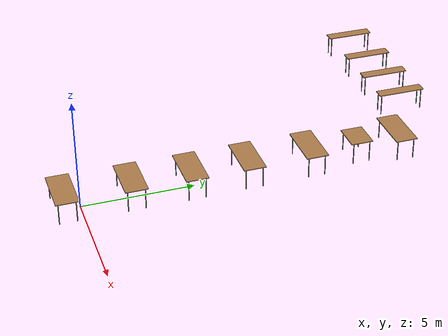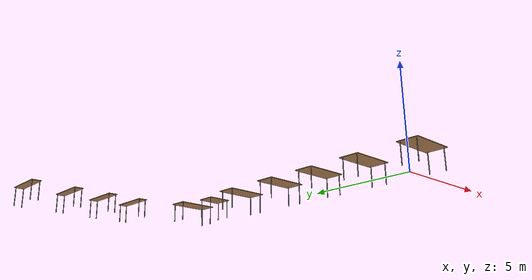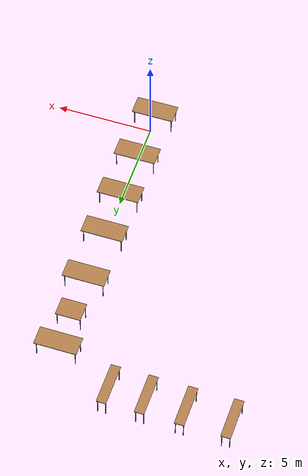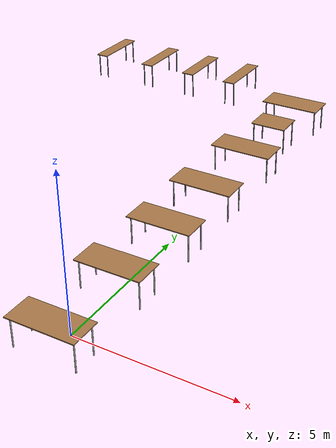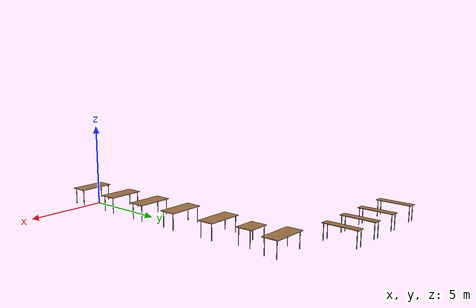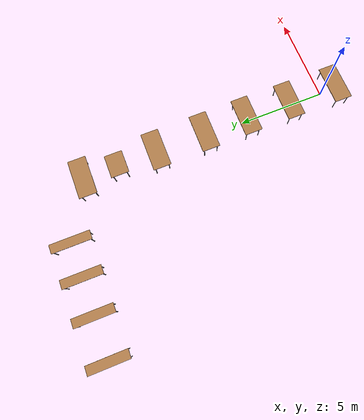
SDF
<?xml version='1.0'?>
<sdf version='1.6'>
  <model name='mi_og'>
    <link name='link_clone'>
      <self_collide>0</self_collide>
      <enable_wind>0</enable_wind>
      <kinematic>0</kinematic>
      <pose frame=''>-0.022325 2.22236 0 0 -0 0</pose>
      <gravity>1</gravity>
      <inertial>
        <mass>1</mass>
        <pose frame=''>0 0 0 0 -0 0</pose>
        <inertia>
          <ixx>1</ixx>
          <ixy>0</ixy>
          <ixz>0</ixz>
          <iyy>1</iyy>
          <iyz>0</iyz>
          <izz>1</izz>
        </inertia>
      </inertial>
      <visual name='front_right_leg'>
        <pose frame=''>1 -0.38 0.5 0 -0 0</pose>
        <geometry>
          <cylinder>
            <radius>0.02</radius>
            <length>1</length>
          </cylinder>
        </geometry>
        <material>
          <script>
            <uri>file://media/materials/scripts/gazebo.material</uri>
            <name>Gazebo/Grey</name>
          </script>
          <shader type='vertex'>
            <normal_map>__default__</normal_map>
          </shader>
          <ambient>0.3 0.3 0.3 1</ambient>
          <diffuse>0.7 0.7 0.7 1</diffuse>
          <specular>0.01 0.01 0.01 1</specular>
          <emissive>0 0 0 1</emissive>
        </material>
        <transparency>0</transparency>
        <cast_shadows>1</cast_shadows>
      </visual>
      <visual name='front_left_leg'>
        <pose frame=''>1 0.38 0.5 0 -0 0</pose>
        <geometry>
          <cylinder>
            <radius>0.02</radius>
            <length>1</length>
          </cylinder>
        </geometry>
        <material>
          <script>
            <uri>file://media/materials/scripts/gazebo.material</uri>
            <name>Gazebo/Grey</name>
          </script>
          <shader type='vertex'>
            <normal_map>__default__</normal_map>
          </shader>
          <ambient>0.3 0.3 0.3 1</ambient>
          <diffuse>0.7 0.7 0.7 1</diffuse>
          <specular>0.01 0.01 0.01 1</specular>
          <emissive>0 0 0 1</emissive>
        </material>
        <transparency>0</transparency>
        <cast_shadows>1</cast_shadows>
      </visual>
      <visual name='visual1'>
        <pose frame=''>0 0 1 0 -0 0</pose>
        <geometry>
          <box>
            <size>2.2 1 0.03</size>
          </box>
        </geometry>
        <material>
          <script>
            <uri>file://media/materials/scripts/gazebo.material</uri>
            <name>Gazebo/Wood</name>
          </script>
          <shader type='vertex'>
            <normal_map>__default__</normal_map>
          </shader>
          <ambient>1 1 1 1</ambient>
          <diffuse>1 1 1 1</diffuse>
          <specular>0.2 0.2 0.2 1</specular>
          <emissive>0 0 0 1</emissive>
        </material>
        <transparency>0</transparency>
        <cast_shadows>1</cast_shadows>
      </visual>
      <visual name='back_right_leg'>
        <pose frame=''>-1 -0.38 0.5 0 -0 0</pose>
        <geometry>
          <cylinder>
            <radius>0.02</radius>
            <length>1</length>
          </cylinder>
        </geometry>
        <material>
          <script>
            <uri>file://media/materials/scripts/gazebo.material</uri>
            <name>Gazebo/Grey</name>
          </script>
          <shader type='vertex'>
            <normal_map>__default__</normal_map>
          </shader>
          <ambient>0.3 0.3 0.3 1</ambient>
          <diffuse>0.7 0.7 0.7 1</diffuse>
          <specular>0.01 0.01 0.01 1</specular>
          <emissive>0 0 0 1</emissive>
        </material>
        <transparency>0</transparency>
        <cast_shadows>1</cast_shadows>
      </visual>
      <visual name='back_left_leg'>
        <pose frame=''>-1 0.38 0.5 0 -0 0</pose>
        <geometry>
          <cylinder>
            <radius>0.02</radius>
            <length>1</length>
          </cylinder>
        </geometry>
        <material>
          <script>
            <uri>file://media/materials/scripts/gazebo.material</uri>
            <name>Gazebo/Grey</name>
          </script>
          <shader type='vertex'>
            <normal_map>__default__</normal_map>
          </shader>
          <ambient>0.3 0.3 0.3 1</ambient>
          <diffuse>0.7 0.7 0.7 1</diffuse>
          <specular>0.01 0.01 0.01 1</specular>
          <emissive>0 0 0 1</emissive>
        </material>
        <transparency>0</transparency>
        <cast_shadows>1</cast_shadows>
      </visual>
      <collision name='surface'>
        <laser_retro>0</laser_retro>
        <max_contacts>10</max_contacts>
        <pose frame=''>0 0 1 0 -0 0</pose>
        <geometry>
          <box>
            <size>2.2 1 0.03</size>
          </box>
        </geometry>
        <surface>
          <friction>
            <ode>
              <mu>1</mu>
              <mu2>1</mu2>
              <fdir1>0 0 0</fdir1>
              <slip1>0</slip1>
              <slip2>0</slip2>
            </ode>
            <torsional>
              <coefficient>1</coefficient>
              <patch_radius>0</patch_radius>
              <surface_radius>0</surface_radius>
              <use_patch_radius>1</use_patch_radius>
              <ode>
                <slip>0</slip>
              </ode>
            </torsional>
          </friction>
          <bounce>
            <restitution_coefficient>0</restitution_coefficient>
            <threshold>1e+06</threshold>
          </bounce>
          <contact>
            <collide_without_contact>0</collide_without_contact>
            <collide_without_contact_bitmask>1</collide_without_contact_bitmask>
            <collide_bitmask>1</collide_bitmask>
            <ode>
              <soft_cfm>0</soft_cfm>
              <soft_erp>0.2</soft_erp>
              <kp>1e+13</kp>
              <kd>1</kd>
              <max_vel>0.01</max_vel>
              <min_depth>0</min_depth>
            </ode>
            <bullet>
              <split_impulse>1</split_impulse>
              <split_impulse_penetration_threshold>-0.01</split_impulse_penetration_threshold>
              <soft_cfm>0</soft_cfm>
              <soft_erp>0.2</soft_erp>
              <kp>1e+13</kp>
              <kd>1</kd>
            </bullet>
          </contact>
        </surface>
      </collision>
      <collision name='front_left_leg_0'>
        <laser_retro>0</laser_retro>
        <max_contacts>10</max_contacts>
        <pose frame=''>1 0.38 0.5 0 -0 0</pose>
        <geometry>
          <cylinder>
            <radius>0.02</radius>
            <length>1</length>
          </cylinder>
        </geometry>
        <surface>
          <friction>
            <ode>
              <mu>1</mu>
              <mu2>1</mu2>
              <fdir1>0 0 0</fdir1>
              <slip1>0</slip1>
              <slip2>0</slip2>
            </ode>
            <torsional>
              <coefficient>1</coefficient>
              <patch_radius>0</patch_radius>
              <surface_radius>0</surface_radius>
              <use_patch_radius>1</use_patch_radius>
              <ode>
                <slip>0</slip>
              </ode>
            </torsional>
          </friction>
          <bounce>
            <restitution_coefficient>0</restitution_coefficient>
            <threshold>1e+06</threshold>
          </bounce>
          <contact>
            <collide_without_contact>0</collide_without_contact>
            <collide_without_contact_bitmask>1</collide_without_contact_bitmask>
            <collide_bitmask>1</collide_bitmask>
            <ode>
              <soft_cfm>0</soft_cfm>
              <soft_erp>0.2</soft_erp>
              <kp>1e+13</kp>
              <kd>1</kd>
              <max_vel>0.01</max_vel>
              <min_depth>0</min_depth>
            </ode>
            <bullet>
              <split_impulse>1</split_impulse>
              <split_impulse_penetration_threshold>-0.01</split_impulse_penetration_threshold>
              <soft_cfm>0</soft_cfm>
              <soft_erp>0.2</soft_erp>
              <kp>1e+13</kp>
              <kd>1</kd>
            </bullet>
          </contact>
        </surface>
      </collision>
      <collision name='front_right_leg_0'>
        <laser_retro>0</laser_retro>
        <max_contacts>10</max_contacts>
        <pose frame=''>1 -0.38 0.5 0 -0 0</pose>
        <geometry>
          <cylinder>
            <radius>0.02</radius>
            <length>1</length>
          </cylinder>
        </geometry>
        <surface>
          <friction>
            <ode>
              <mu>1</mu>
              <mu2>1</mu2>
              <fdir1>0 0 0</fdir1>
              <slip1>0</slip1>
              <slip2>0</slip2>
            </ode>
            <torsional>
              <coefficient>1</coefficient>
              <patch_radius>0</patch_radius>
              <surface_radius>0</surface_radius>
              <use_patch_radius>1</use_patch_radius>
              <ode>
                <slip>0</slip>
              </ode>
            </torsional>
          </friction>
          <bounce>
            <restitution_coefficient>0</restitution_coefficient>
            <threshold>1e+06</threshold>
          </bounce>
          <contact>
            <collide_without_contact>0</collide_without_contact>
            <collide_without_contact_bitmask>1</collide_without_contact_bitmask>
            <collide_bitmask>1</collide_bitmask>
            <ode>
              <soft_cfm>0</soft_cfm>
              <soft_erp>0.2</soft_erp>
              <kp>1e+13</kp>
              <kd>1</kd>
              <max_vel>0.01</max_vel>
              <min_depth>0</min_depth>
            </ode>
            <bullet>
              <split_impulse>1</split_impulse>
              <split_impulse_penetration_threshold>-0.01</split_impulse_penetration_threshold>
              <soft_cfm>0</soft_cfm>
              <soft_erp>0.2</soft_erp>
              <kp>1e+13</kp>
              <kd>1</kd>
            </bullet>
          </contact>
        </surface>
      </collision>
      <collision name='back_left_leg_0'>
        <laser_retro>0</laser_retro>
        <max_contacts>10</max_contacts>
        <pose frame=''>-1 0.38 0.5 0 -0 0</pose>
        <geometry>
          <cylinder>
            <radius>0.02</radius>
            <length>1</length>
          </cylinder>
        </geometry>
        <surface>
          <friction>
            <ode>
              <mu>1</mu>
              <mu2>1</mu2>
              <fdir1>0 0 0</fdir1>
              <slip1>0</slip1>
              <slip2>0</slip2>
            </ode>
            <torsional>
              <coefficient>1</coefficient>
              <patch_radius>0</patch_radius>
              <surface_radius>0</surface_radius>
              <use_patch_radius>1</use_patch_radius>
              <ode>
                <slip>0</slip>
              </ode>
            </torsional>
          </friction>
          <bounce>
            <restitution_coefficient>0</restitution_coefficient>
            <threshold>1e+06</threshold>
          </bounce>
          <contact>
            <collide_without_contact>0</collide_without_contact>
            <collide_without_contact_bitmask>1</collide_without_contact_bitmask>
            <collide_bitmask>1</collide_bitmask>
            <ode>
              <soft_cfm>0</soft_cfm>
              <soft_erp>0.2</soft_erp>
              <kp>1e+13</kp>
              <kd>1</kd>
              <max_vel>0.01</max_vel>
              <min_depth>0</min_depth>
            </ode>
            <bullet>
              <split_impulse>1</split_impulse>
              <split_impulse_penetration_threshold>-0.01</split_impulse_penetration_threshold>
              <soft_cfm>0</soft_cfm>
              <soft_erp>0.2</soft_erp>
              <kp>1e+13</kp>
              <kd>1</kd>
            </bullet>
          </contact>
        </surface>
      </collision>
      <collision name='back_right_leg_0'>
        <laser_retro>0</laser_retro>
        <max_contacts>10</max_contacts>
        <pose frame=''>-1 -0.38 0.5 0 -0 0</pose>
        <geometry>
          <cylinder>
            <radius>0.02</radius>
            <length>1</length>
          </cylinder>
        </geometry>
        <surface>
          <friction>
            <ode>
              <mu>1</mu>
              <mu2>1</mu2>
              <fdir1>0 0 0</fdir1>
              <slip1>0</slip1>
              <slip2>0</slip2>
            </ode>
            <torsional>
              <coefficient>1</coefficient>
              <patch_radius>0</patch_radius>
              <surface_radius>0</surface_radius>
              <use_patch_radius>1</use_patch_radius>
              <ode>
                <slip>0</slip>
              </ode>
            </torsional>
          </friction>
          <bounce>
            <restitution_coefficient>0</restitution_coefficient>
            <threshold>1e+06</threshold>
          </bounce>
          <contact>
            <collide_without_contact>0</collide_without_contact>
            <collide_without_contact_bitmask>1</collide_without_contact_bitmask>
            <collide_bitmask>1</collide_bitmask>
            <ode>
              <soft_cfm>0</soft_cfm>
              <soft_erp>0.2</soft_erp>
              <kp>1e+13</kp>
              <kd>1</kd>
              <max_vel>0.01</max_vel>
              <min_depth>0</min_depth>
            </ode>
            <bullet>
              <split_impulse>1</split_impulse>
              <split_impulse_penetration_threshold>-0.01</split_impulse_penetration_threshold>
              <soft_cfm>0</soft_cfm>
              <soft_erp>0.2</soft_erp>
              <kp>1e+13</kp>
              <kd>1</kd>
            </bullet>
          </contact>
        </surface>
      </collision>
    </link>
    <link name='link_clone_0'>
      <self_collide>0</self_collide>
      <enable_wind>0</enable_wind>
      <kinematic>0</kinematic>
      <pose frame=''>-0.000595 4.85022 0 0 -0 0</pose>
      <gravity>1</gravity>
      <inertial>
        <mass>1</mass>
        <pose frame=''>0 0 0 0 -0 0</pose>
        <inertia>
          <ixx>1</ixx>
          <ixy>0</ixy>
          <ixz>0</ixz>
          <iyy>1</iyy>
          <iyz>0</iyz>
          <izz>1</izz>
        </inertia>
      </inertial>
      <visual name='front_left_leg'>
        <pose frame=''>1 0.38 0.5 0 -0 0</pose>
        <geometry>
          <cylinder>
            <radius>0.02</radius>
            <length>1</length>
          </cylinder>
        </geometry>
        <material>
          <script>
            <uri>file://media/materials/scripts/gazebo.material</uri>
            <name>Gazebo/Grey</name>
          </script>
          <shader type='vertex'>
            <normal_map>__default__</normal_map>
          </shader>
          <ambient>0.3 0.3 0.3 1</ambient>
          <diffuse>0.7 0.7 0.7 1</diffuse>
          <specular>0.01 0.01 0.01 1</specular>
          <emissive>0 0 0 1</emissive>
        </material>
        <transparency>0</transparency>
        <cast_shadows>1</cast_shadows>
      </visual>
      <visual name='front_right_leg'>
        <pose frame=''>1 -0.38 0.5 0 -0 0</pose>
        <geometry>
          <cylinder>
            <radius>0.02</radius>
            <length>1</length>
          </cylinder>
        </geometry>
        <material>
          <script>
            <uri>file://media/materials/scripts/gazebo.material</uri>
            <name>Gazebo/Grey</name>
          </script>
          <shader type='vertex'>
            <normal_map>__default__</normal_map>
          </shader>
          <ambient>0.3 0.3 0.3 1</ambient>
          <diffuse>0.7 0.7 0.7 1</diffuse>
          <specular>0.01 0.01 0.01 1</specular>
          <emissive>0 0 0 1</emissive>
        </material>
        <transparency>0</transparency>
        <cast_shadows>1</cast_shadows>
      </visual>
      <visual name='back_right_leg'>
        <pose frame=''>-1 -0.38 0.5 0 -0 0</pose>
        <geometry>
          <cylinder>
            <radius>0.02</radius>
            <length>1</length>
          </cylinder>
        </geometry>
        <material>
          <script>
            <uri>file://media/materials/scripts/gazebo.material</uri>
            <name>Gazebo/Grey</name>
          </script>
          <shader type='vertex'>
            <normal_map>__default__</normal_map>
          </shader>
          <ambient>0.3 0.3 0.3 1</ambient>
          <diffuse>0.7 0.7 0.7 1</diffuse>
          <specular>0.01 0.01 0.01 1</specular>
          <emissive>0 0 0 1</emissive>
        </material>
        <transparency>0</transparency>
        <cast_shadows>1</cast_shadows>
      </visual>
      <visual name='back_left_leg'>
        <pose frame=''>-1 0.38 0.5 0 -0 0</pose>
        <geometry>
          <cylinder>
            <radius>0.02</radius>
            <length>1</length>
          </cylinder>
        </geometry>
        <material>
          <script>
            <uri>file://media/materials/scripts/gazebo.material</uri>
            <name>Gazebo/Grey</name>
          </script>
          <shader type='vertex'>
            <normal_map>__default__</normal_map>
          </shader>
          <ambient>0.3 0.3 0.3 1</ambient>
          <diffuse>0.7 0.7 0.7 1</diffuse>
          <specular>0.01 0.01 0.01 1</specular>
          <emissive>0 0 0 1</emissive>
        </material>
        <transparency>0</transparency>
        <cast_shadows>1</cast_shadows>
      </visual>
      <visual name='visual1'>
        <pose frame=''>0 0 1 0 -0 0</pose>
        <geometry>
          <box>
            <size>2.2 1 0.03</size>
          </box>
        </geometry>
        <material>
          <script>
            <uri>file://media/materials/scripts/gazebo.material</uri>
            <name>Gazebo/Wood</name>
          </script>
          <shader type='vertex'>
            <normal_map>__default__</normal_map>
          </shader>
          <ambient>1 1 1 1</ambient>
          <diffuse>1 1 1 1</diffuse>
          <specular>0.2 0.2 0.2 1</specular>
          <emissive>0 0 0 1</emissive>
        </material>
        <transparency>0</transparency>
        <cast_shadows>1</cast_shadows>
      </visual>
      <collision name='surface'>
        <laser_retro>0</laser_retro>
        <max_contacts>10</max_contacts>
        <pose frame=''>0 0 1 0 -0 0</pose>
        <geometry>
          <box>
            <size>2.2 1 0.03</size>
          </box>
        </geometry>
        <surface>
          <friction>
            <ode>
              <mu>1</mu>
              <mu2>1</mu2>
              <fdir1>0 0 0</fdir1>
              <slip1>0</slip1>
              <slip2>0</slip2>
            </ode>
            <torsional>
              <coefficient>1</coefficient>
              <patch_radius>0</patch_radius>
              <surface_radius>0</surface_radius>
              <use_patch_radius>1</use_patch_radius>
              <ode>
                <slip>0</slip>
              </ode>
            </torsional>
          </friction>
          <bounce>
            <restitution_coefficient>0</restitution_coefficient>
            <threshold>1e+06</threshold>
          </bounce>
          <contact>
            <collide_without_contact>0</collide_without_contact>
            <collide_without_contact_bitmask>1</collide_without_contact_bitmask>
            <collide_bitmask>1</collide_bitmask>
            <ode>
              <soft_cfm>0</soft_cfm>
              <soft_erp>0.2</soft_erp>
              <kp>1e+13</kp>
              <kd>1</kd>
              <max_vel>0.01</max_vel>
              <min_depth>0</min_depth>
            </ode>
            <bullet>
              <split_impulse>1</split_impulse>
              <split_impulse_penetration_threshold>-0.01</split_impulse_penetration_threshold>
              <soft_cfm>0</soft_cfm>
              <soft_erp>0.2</soft_erp>
              <kp>1e+13</kp>
              <kd>1</kd>
            </bullet>
          </contact>
        </surface>
      </collision>
      <collision name='front_left_leg_0'>
        <laser_retro>0</laser_retro>
        <max_contacts>10</max_contacts>
        <pose frame=''>1 0.38 0.5 0 -0 0</pose>
        <geometry>
          <cylinder>
            <radius>0.02</radius>
            <length>1</length>
          </cylinder>
        </geometry>
        <surface>
          <friction>
            <ode>
              <mu>1</mu>
              <mu2>1</mu2>
              <fdir1>0 0 0</fdir1>
              <slip1>0</slip1>
              <slip2>0</slip2>
            </ode>
            <torsional>
              <coefficient>1</coefficient>
              <patch_radius>0</patch_radius>
              <surface_radius>0</surface_radius>
              <use_patch_radius>1</use_patch_radius>
              <ode>
                <slip>0</slip>
              </ode>
            </torsional>
          </friction>
          <bounce>
            <restitution_coefficient>0</restitution_coefficient>
            <threshold>1e+06</threshold>
          </bounce>
          <contact>
            <collide_without_contact>0</collide_without_contact>
            <collide_without_contact_bitmask>1</collide_without_contact_bitmask>
            <collide_bitmask>1</collide_bitmask>
            <ode>
              <soft_cfm>0</soft_cfm>
              <soft_erp>0.2</soft_erp>
              <kp>1e+13</kp>
              <kd>1</kd>
              <max_vel>0.01</max_vel>
              <min_depth>0</min_depth>
            </ode>
            <bullet>
              <split_impulse>1</split_impulse>
              <split_impulse_penetration_threshold>-0.01</split_impulse_penetration_threshold>
              <soft_cfm>0</soft_cfm>
              <soft_erp>0.2</soft_erp>
              <kp>1e+13</kp>
              <kd>1</kd>
            </bullet>
          </contact>
        </surface>
      </collision>
      <collision name='front_right_leg_0'>
        <laser_retro>0</laser_retro>
        <max_contacts>10</max_contacts>
        <pose frame=''>1 -0.38 0.5 0 -0 0</pose>
        <geometry>
          <cylinder>
            <radius>0.02</radius>
            <length>1</length>
          </cylinder>
        </geometry>
        <surface>
          <friction>
            <ode>
              <mu>1</mu>
              <mu2>1</mu2>
              <fdir1>0 0 0</fdir1>
              <slip1>0</slip1>
              <slip2>0</slip2>
            </ode>
            <torsional>
              <coefficient>1</coefficient>
              <patch_radius>0</patch_radius>
              <surface_radius>0</surface_radius>
              <use_patch_radius>1</use_patch_radius>
              <ode>
                <slip>0</slip>
              </ode>
            </torsional>
          </friction>
          <bounce>
            <restitution_coefficient>0</restitution_coefficient>
            <threshold>1e+06</threshold>
          </bounce>
          <contact>
            <collide_without_contact>0</collide_without_contact>
            <collide_without_contact_bitmask>1</collide_without_contact_bitmask>
            <collide_bitmask>1</collide_bitmask>
            <ode>
              <soft_cfm>0</soft_cfm>
              <soft_erp>0.2</soft_erp>
              <kp>1e+13</kp>
              <kd>1</kd>
              <max_vel>0.01</max_vel>
              <min_depth>0</min_depth>
            </ode>
            <bullet>
              <split_impulse>1</split_impulse>
              <split_impulse_penetration_threshold>-0.01</split_impulse_penetration_threshold>
              <soft_cfm>0</soft_cfm>
              <soft_erp>0.2</soft_erp>
              <kp>1e+13</kp>
              <kd>1</kd>
            </bullet>
          </contact>
        </surface>
      </collision>
      <collision name='back_right_leg_0'>
        <laser_retro>0</laser_retro>
        <max_contacts>10</max_contacts>
        <pose frame=''>-1 -0.38 0.5 0 -0 0</pose>
        <geometry>
          <cylinder>
            <radius>0.02</radius>
            <length>1</length>
          </cylinder>
        </geometry>
        <surface>
          <friction>
            <ode>
              <mu>1</mu>
              <mu2>1</mu2>
              <fdir1>0 0 0</fdir1>
              <slip1>0</slip1>
              <slip2>0</slip2>
            </ode>
            <torsional>
              <coefficient>1</coefficient>
              <patch_radius>0</patch_radius>
              <surface_radius>0</surface_radius>
              <use_patch_radius>1</use_patch_radius>
              <ode>
                <slip>0</slip>
              </ode>
            </torsional>
          </friction>
          <bounce>
            <restitution_coefficient>0</restitution_coefficient>
            <threshold>1e+06</threshold>
          </bounce>
          <contact>
            <collide_without_contact>0</collide_without_contact>
            <collide_without_contact_bitmask>1</collide_without_contact_bitmask>
            <collide_bitmask>1</collide_bitmask>
            <ode>
              <soft_cfm>0</soft_cfm>
              <soft_erp>0.2</soft_erp>
              <kp>1e+13</kp>
              <kd>1</kd>
              <max_vel>0.01</max_vel>
              <min_depth>0</min_depth>
            </ode>
            <bullet>
              <split_impulse>1</split_impulse>
              <split_impulse_penetration_threshold>-0.01</split_impulse_penetration_threshold>
              <soft_cfm>0</soft_cfm>
              <soft_erp>0.2</soft_erp>
              <kp>1e+13</kp>
              <kd>1</kd>
            </bullet>
          </contact>
        </surface>
      </collision>
      <collision name='back_left_leg_0'>
        <laser_retro>0</laser_retro>
        <max_contacts>10</max_contacts>
        <pose frame=''>-1 0.38 0.5 0 -0 0</pose>
        <geometry>
          <cylinder>
            <radius>0.02</radius>
            <length>1</length>
          </cylinder>
        </geometry>
        <surface>
          <friction>
            <ode>
              <mu>1</mu>
              <mu2>1</mu2>
              <fdir1>0 0 0</fdir1>
              <slip1>0</slip1>
              <slip2>0</slip2>
            </ode>
            <torsional>
              <coefficient>1</coefficient>
              <patch_radius>0</patch_radius>
              <surface_radius>0</surface_radius>
              <use_patch_radius>1</use_patch_radius>
              <ode>
                <slip>0</slip>
              </ode>
            </torsional>
          </friction>
          <bounce>
            <restitution_coefficient>0</restitution_coefficient>
            <threshold>1e+06</threshold>
          </bounce>
          <contact>
            <collide_without_contact>0</collide_without_contact>
            <collide_without_contact_bitmask>1</collide_without_contact_bitmask>
            <collide_bitmask>1</collide_bitmask>
            <ode>
              <soft_cfm>0</soft_cfm>
              <soft_erp>0.2</soft_erp>
              <kp>1e+13</kp>
              <kd>1</kd>
              <max_vel>0.01</max_vel>
              <min_depth>0</min_depth>
            </ode>
            <bullet>
              <split_impulse>1</split_impulse>
              <split_impulse_penetration_threshold>-0.01</split_impulse_penetration_threshold>
              <soft_cfm>0</soft_cfm>
              <soft_erp>0.2</soft_erp>
              <kp>1e+13</kp>
              <kd>1</kd>
            </bullet>
          </contact>
        </surface>
      </collision>
    </link>
    <link name='link_clone_1'>
      <self_collide>0</self_collide>
      <enable_wind>0</enable_wind>
      <kinematic>0</kinematic>
      <pose frame=''>-0.024672 7.41051 0 0 -0 0</pose>
      <gravity>1</gravity>
      <inertial>
        <mass>1</mass>
        <pose frame=''>0 0 0 0 -0 0</pose>
        <inertia>
          <ixx>1</ixx>
          <ixy>0</ixy>
          <ixz>0</ixz>
          <iyy>1</iyy>
          <iyz>0</iyz>
          <izz>1</izz>
        </inertia>
      </inertial>
      <visual name='visual1'>
        <pose frame=''>0 0 1 0 -0 0</pose>
        <geometry>
          <box>
            <size>2.2 1 0.03</size>
          </box>
        </geometry>
        <material>
          <script>
            <uri>file://media/materials/scripts/gazebo.material</uri>
            <name>Gazebo/Wood</name>
          </script>
          <shader type='vertex'>
            <normal_map>__default__</normal_map>
          </shader>
          <ambient>1 1 1 1</ambient>
          <diffuse>1 1 1 1</diffuse>
          <specular>0.2 0.2 0.2 1</specular>
          <emissive>0 0 0 1</emissive>
        </material>
        <transparency>0</transparency>
        <cast_shadows>1</cast_shadows>
      </visual>
      <visual name='front_left_leg'>
        <pose frame=''>1 0.38 0.5 0 -0 0</pose>
        <geometry>
          <cylinder>
            <radius>0.02</radius>
            <length>1</length>
          </cylinder>
        </geometry>
        <material>
          <script>
            <uri>file://media/materials/scripts/gazebo.material</uri>
            <name>Gazebo/Grey</name>
          </script>
          <shader type='vertex'>
            <normal_map>__default__</normal_map>
          </shader>
          <ambient>0.3 0.3 0.3 1</ambient>
          <diffuse>0.7 0.7 0.7 1</diffuse>
          <specular>0.01 0.01 0.01 1</specular>
          <emissive>0 0 0 1</emissive>
        </material>
        <transparency>0</transparency>
        <cast_shadows>1</cast_shadows>
      </visual>
      <visual name='front_right_leg'>
        <pose frame=''>1 -0.38 0.5 0 -0 0</pose>
        <geometry>
          <cylinder>
            <radius>0.02</radius>
            <length>1</length>
          </cylinder>
        </geometry>
        <material>
          <script>
            <uri>file://media/materials/scripts/gazebo.material</uri>
            <name>Gazebo/Grey</name>
          </script>
          <shader type='vertex'>
            <normal_map>__default__</normal_map>
          </shader>
          <ambient>0.3 0.3 0.3 1</ambient>
          <diffuse>0.7 0.7 0.7 1</diffuse>
          <specular>0.01 0.01 0.01 1</specular>
          <emissive>0 0 0 1</emissive>
        </material>
        <transparency>0</transparency>
        <cast_shadows>1</cast_shadows>
      </visual>
      <visual name='back_right_leg'>
        <pose frame=''>-1 -0.38 0.5 0 -0 0</pose>
        <geometry>
          <cylinder>
            <radius>0.02</radius>
            <length>1</length>
          </cylinder>
        </geometry>
        <material>
          <script>
            <uri>file://media/materials/scripts/gazebo.material</uri>
            <name>Gazebo/Grey</name>
          </script>
          <shader type='vertex'>
            <normal_map>__default__</normal_map>
          </shader>
          <ambient>0.3 0.3 0.3 1</ambient>
          <diffuse>0.7 0.7 0.7 1</diffuse>
          <specular>0.01 0.01 0.01 1</specular>
          <emissive>0 0 0 1</emissive>
        </material>
        <transparency>0</transparency>
        <cast_shadows>1</cast_shadows>
      </visual>
      <visual name='back_left_leg'>
        <pose frame=''>-1 0.38 0.5 0 -0 0</pose>
        <geometry>
          <cylinder>
            <radius>0.02</radius>
            <length>1</length>
          </cylinder>
        </geometry>
        <material>
          <script>
            <uri>file://media/materials/scripts/gazebo.material</uri>
            <name>Gazebo/Grey</name>
          </script>
          <shader type='vertex'>
            <normal_map>__default__</normal_map>
          </shader>
          <ambient>0.3 0.3 0.3 1</ambient>
          <diffuse>0.7 0.7 0.7 1</diffuse>
          <specular>0.01 0.01 0.01 1</specular>
          <emissive>0 0 0 1</emissive>
        </material>
        <transparency>0</transparency>
        <cast_shadows>1</cast_shadows>
      </visual>
      <collision name='surface'>
        <laser_retro>0</laser_retro>
        <max_contacts>10</max_contacts>
        <pose frame=''>0 0 1 0 -0 0</pose>
        <geometry>
          <box>
            <size>2.2 1 0.03</size>
          </box>
        </geometry>
        <surface>
          <friction>
            <ode>
              <mu>1</mu>
              <mu2>1</mu2>
              <fdir1>0 0 0</fdir1>
              <slip1>0</slip1>
              <slip2>0</slip2>
            </ode>
            <torsional>
              <coefficient>1</coefficient>
              <patch_radius>0</patch_radius>
              <surface_radius>0</surface_radius>
              <use_patch_radius>1</use_patch_radius>
              <ode>
                <slip>0</slip>
              </ode>
            </torsional>
          </friction>
          <bounce>
            <restitution_coefficient>0</restitution_coefficient>
            <threshold>1e+06</threshold>
          </bounce>
          <contact>
            <collide_without_contact>0</collide_without_contact>
            <collide_without_contact_bitmask>1</collide_without_contact_bitmask>
            <collide_bitmask>1</collide_bitmask>
            <ode>
              <soft_cfm>0</soft_cfm>
              <soft_erp>0.2</soft_erp>
              <kp>1e+13</kp>
              <kd>1</kd>
              <max_vel>0.01</max_vel>
              <min_depth>0</min_depth>
            </ode>
            <bullet>
              <split_impulse>1</split_impulse>
              <split_impulse_penetration_threshold>-0.01</split_impulse_penetration_threshold>
              <soft_cfm>0</soft_cfm>
              <soft_erp>0.2</soft_erp>
              <kp>1e+13</kp>
              <kd>1</kd>
            </bullet>
          </contact>
        </surface>
      </collision>
      <collision name='front_left_leg_0'>
        <laser_retro>0</laser_retro>
        <max_contacts>10</max_contacts>
        <pose frame=''>1 0.38 0.5 0 -0 0</pose>
        <geometry>
          <cylinder>
            <radius>0.02</radius>
            <length>1</length>
          </cylinder>
        </geometry>
        <surface>
          <friction>
            <ode>
              <mu>1</mu>
              <mu2>1</mu2>
              <fdir1>0 0 0</fdir1>
              <slip1>0</slip1>
              <slip2>0</slip2>
            </ode>
            <torsional>
              <coefficient>1</coefficient>
              <patch_radius>0</patch_radius>
              <surface_radius>0</surface_radius>
              <use_patch_radius>1</use_patch_radius>
              <ode>
                <slip>0</slip>
              </ode>
            </torsional>
          </friction>
          <bounce>
            <restitution_coefficient>0</restitution_coefficient>
            <threshold>1e+06</threshold>
          </bounce>
          <contact>
            <collide_without_contact>0</collide_without_contact>
            <collide_without_contact_bitmask>1</collide_without_contact_bitmask>
            <collide_bitmask>1</collide_bitmask>
            <ode>
              <soft_cfm>0</soft_cfm>
              <soft_erp>0.2</soft_erp>
              <kp>1e+13</kp>
              <kd>1</kd>
              <max_vel>0.01</max_vel>
              <min_depth>0</min_depth>
            </ode>
            <bullet>
              <split_impulse>1</split_impulse>
              <split_impulse_penetration_threshold>-0.01</split_impulse_penetration_threshold>
              <soft_cfm>0</soft_cfm>
              <soft_erp>0.2</soft_erp>
              <kp>1e+13</kp>
              <kd>1</kd>
            </bullet>
          </contact>
        </surface>
      </collision>
      <collision name='front_right_leg_0'>
        <laser_retro>0</laser_retro>
        <max_contacts>10</max_contacts>
        <pose frame=''>1 -0.38 0.5 0 -0 0</pose>
        <geometry>
          <cylinder>
            <radius>0.02</radius>
            <length>1</length>
          </cylinder>
        </geometry>
        <surface>
          <friction>
            <ode>
              <mu>1</mu>
              <mu2>1</mu2>
              <fdir1>0 0 0</fdir1>
              <slip1>0</slip1>
              <slip2>0</slip2>
            </ode>
            <torsional>
              <coefficient>1</coefficient>
              <patch_radius>0</patch_radius>
              <surface_radius>0</surface_radius>
              <use_patch_radius>1</use_patch_radius>
              <ode>
                <slip>0</slip>
              </ode>
            </torsional>
          </friction>
          <bounce>
            <restitution_coefficient>0</restitution_coefficient>
            <threshold>1e+06</threshold>
          </bounce>
          <contact>
            <collide_without_contact>0</collide_without_contact>
            <collide_without_contact_bitmask>1</collide_without_contact_bitmask>
            <collide_bitmask>1</collide_bitmask>
            <ode>
              <soft_cfm>0</soft_cfm>
              <soft_erp>0.2</soft_erp>
              <kp>1e+13</kp>
              <kd>1</kd>
              <max_vel>0.01</max_vel>
              <min_depth>0</min_depth>
            </ode>
            <bullet>
              <split_impulse>1</split_impulse>
              <split_impulse_penetration_threshold>-0.01</split_impulse_penetration_threshold>
              <soft_cfm>0</soft_cfm>
              <soft_erp>0.2</soft_erp>
              <kp>1e+13</kp>
              <kd>1</kd>
            </bullet>
          </contact>
        </surface>
      </collision>
      <collision name='back_right_leg_0'>
        <laser_retro>0</laser_retro>
        <max_contacts>10</max_contacts>
        <pose frame=''>-1 -0.38 0.5 0 -0 0</pose>
        <geometry>
          <cylinder>
            <radius>0.02</radius>
            <length>1</length>
          </cylinder>
        </geometry>
        <surface>
          <friction>
            <ode>
              <mu>1</mu>
              <mu2>1</mu2>
              <fdir1>0 0 0</fdir1>
              <slip1>0</slip1>
              <slip2>0</slip2>
            </ode>
            <torsional>
              <coefficient>1</coefficient>
              <patch_radius>0</patch_radius>
              <surface_radius>0</surface_radius>
              <use_patch_radius>1</use_patch_radius>
              <ode>
                <slip>0</slip>
              </ode>
            </torsional>
          </friction>
          <bounce>
            <restitution_coefficient>0</restitution_coefficient>
            <threshold>1e+06</threshold>
          </bounce>
          <contact>
            <collide_without_contact>0</collide_without_contact>
            <collide_without_contact_bitmask>1</collide_without_contact_bitmask>
            <collide_bitmask>1</collide_bitmask>
            <ode>
              <soft_cfm>0</soft_cfm>
              <soft_erp>0.2</soft_erp>
              <kp>1e+13</kp>
              <kd>1</kd>
              <max_vel>0.01</max_vel>
              <min_depth>0</min_depth>
            </ode>
            <bullet>
              <split_impulse>1</split_impulse>
              <split_impulse_penetration_threshold>-0.01</split_impulse_penetration_threshold>
              <soft_cfm>0</soft_cfm>
              <soft_erp>0.2</soft_erp>
              <kp>1e+13</kp>
              <kd>1</kd>
            </bullet>
          </contact>
        </surface>
      </collision>
      <collision name='back_left_leg_0'>
        <laser_retro>0</laser_retro>
        <max_contacts>10</max_contacts>
        <pose frame=''>-1 0.38 0.5 0 -0 0</pose>
        <geometry>
          <cylinder>
            <radius>0.02</radius>
            <length>1</length>
          </cylinder>
        </geometry>
        <surface>
          <friction>
            <ode>
              <mu>1</mu>
              <mu2>1</mu2>
              <fdir1>0 0 0</fdir1>
              <slip1>0</slip1>
              <slip2>0</slip2>
            </ode>
            <torsional>
              <coefficient>1</coefficient>
              <patch_radius>0</patch_radius>
              <surface_radius>0</surface_radius>
              <use_patch_radius>1</use_patch_radius>
              <ode>
                <slip>0</slip>
              </ode>
            </torsional>
          </friction>
          <bounce>
            <restitution_coefficient>0</restitution_coefficient>
            <threshold>1e+06</threshold>
          </bounce>
          <contact>
            <collide_without_contact>0</collide_without_contact>
            <collide_without_contact_bitmask>1</collide_without_contact_bitmask>
            <collide_bitmask>1</collide_bitmask>
            <ode>
              <soft_cfm>0</soft_cfm>
              <soft_erp>0.2</soft_erp>
              <kp>1e+13</kp>
              <kd>1</kd>
              <max_vel>0.01</max_vel>
              <min_depth>0</min_depth>
            </ode>
            <bullet>
              <split_impulse>1</split_impulse>
              <split_impulse_penetration_threshold>-0.01</split_impulse_penetration_threshold>
              <soft_cfm>0</soft_cfm>
              <soft_erp>0.2</soft_erp>
              <kp>1e+13</kp>
              <kd>1</kd>
            </bullet>
          </contact>
        </surface>
      </collision>
    </link>
    <link name='link_clone_2'>
      <self_collide>0</self_collide>
      <enable_wind>0</enable_wind>
      <kinematic>0</kinematic>
      <pose frame=''>-0.032705 10.2761 0 0 -0 0</pose>
      <gravity>1</gravity>
      <inertial>
        <mass>1</mass>
        <pose frame=''>0 0 0 0 -0 0</pose>
        <inertia>
          <ixx>1</ixx>
          <ixy>0</ixy>
          <ixz>0</ixz>
          <iyy>1</iyy>
          <iyz>0</iyz>
          <izz>1</izz>
        </inertia>
      </inertial>
      <visual name='visual1'>
        <pose frame=''>0 0 1 0 -0 0</pose>
        <geometry>
          <box>
            <size>2.2 1 0.03</size>
          </box>
        </geometry>
        <material>
          <script>
            <uri>file://media/materials/scripts/gazebo.material</uri>
            <name>Gazebo/Wood</name>
          </script>
          <shader type='vertex'>
            <normal_map>__default__</normal_map>
          </shader>
          <ambient>1 1 1 1</ambient>
          <diffuse>1 1 1 1</diffuse>
          <specular>0.2 0.2 0.2 1</specular>
          <emissive>0 0 0 1</emissive>
        </material>
        <transparency>0</transparency>
        <cast_shadows>1</cast_shadows>
      </visual>
      <visual name='front_left_leg'>
        <pose frame=''>1 0.38 0.5 0 -0 0</pose>
        <geometry>
          <cylinder>
            <radius>0.02</radius>
            <length>1</length>
          </cylinder>
        </geometry>
        <material>
          <script>
            <uri>file://media/materials/scripts/gazebo.material</uri>
            <name>Gazebo/Grey</name>
          </script>
          <shader type='vertex'>
            <normal_map>__default__</normal_map>
          </shader>
          <ambient>0.3 0.3 0.3 1</ambient>
          <diffuse>0.7 0.7 0.7 1</diffuse>
          <specular>0.01 0.01 0.01 1</specular>
          <emissive>0 0 0 1</emissive>
        </material>
        <transparency>0</transparency>
        <cast_shadows>1</cast_shadows>
      </visual>
      <visual name='front_right_leg'>
        <pose frame=''>1 -0.38 0.5 0 -0 0</pose>
        <geometry>
          <cylinder>
            <radius>0.02</radius>
            <length>1</length>
          </cylinder>
        </geometry>
        <material>
          <script>
            <uri>file://media/materials/scripts/gazebo.material</uri>
            <name>Gazebo/Grey</name>
          </script>
          <shader type='vertex'>
            <normal_map>__default__</normal_map>
          </shader>
          <ambient>0.3 0.3 0.3 1</ambient>
          <diffuse>0.7 0.7 0.7 1</diffuse>
          <specular>0.01 0.01 0.01 1</specular>
          <emissive>0 0 0 1</emissive>
        </material>
        <transparency>0</transparency>
        <cast_shadows>1</cast_shadows>
      </visual>
      <visual name='back_right_leg'>
        <pose frame=''>-1 -0.38 0.5 0 -0 0</pose>
        <geometry>
          <cylinder>
            <radius>0.02</radius>
            <length>1</length>
          </cylinder>
        </geometry>
        <material>
          <script>
            <uri>file://media/materials/scripts/gazebo.material</uri>
            <name>Gazebo/Grey</name>
          </script>
          <shader type='vertex'>
            <normal_map>__default__</normal_map>
          </shader>
          <ambient>0.3 0.3 0.3 1</ambient>
          <diffuse>0.7 0.7 0.7 1</diffuse>
          <specular>0.01 0.01 0.01 1</specular>
          <emissive>0 0 0 1</emissive>
        </material>
        <transparency>0</transparency>
        <cast_shadows>1</cast_shadows>
      </visual>
      <visual name='back_left_leg'>
        <pose frame=''>-1 0.38 0.5 0 -0 0</pose>
        <geometry>
          <cylinder>
            <radius>0.02</radius>
            <length>1</length>
          </cylinder>
        </geometry>
        <material>
          <script>
            <uri>file://media/materials/scripts/gazebo.material</uri>
            <name>Gazebo/Grey</name>
          </script>
          <shader type='vertex'>
            <normal_map>__default__</normal_map>
          </shader>
          <ambient>0.3 0.3 0.3 1</ambient>
          <diffuse>0.7 0.7 0.7 1</diffuse>
          <specular>0.01 0.01 0.01 1</specular>
          <emissive>0 0 0 1</emissive>
        </material>
        <transparency>0</transparency>
        <cast_shadows>1</cast_shadows>
      </visual>
      <collision name='surface'>
        <laser_retro>0</laser_retro>
        <max_contacts>10</max_contacts>
        <pose frame=''>0 0 1 0 -0 0</pose>
        <geometry>
          <box>
            <size>2.2 1 0.03</size>
          </box>
        </geometry>
        <surface>
          <friction>
            <ode>
              <mu>1</mu>
              <mu2>1</mu2>
              <fdir1>0 0 0</fdir1>
              <slip1>0</slip1>
              <slip2>0</slip2>
            </ode>
            <torsional>
              <coefficient>1</coefficient>
              <patch_radius>0</patch_radius>
              <surface_radius>0</surface_radius>
              <use_patch_radius>1</use_patch_radius>
              <ode>
                <slip>0</slip>
              </ode>
            </torsional>
          </friction>
          <bounce>
            <restitution_coefficient>0</restitution_coefficient>
            <threshold>1e+06</threshold>
          </bounce>
          <contact>
            <collide_without_contact>0</collide_without_contact>
            <collide_without_contact_bitmask>1</collide_without_contact_bitmask>
            <collide_bitmask>1</collide_bitmask>
            <ode>
              <soft_cfm>0</soft_cfm>
              <soft_erp>0.2</soft_erp>
              <kp>1e+13</kp>
              <kd>1</kd>
              <max_vel>0.01</max_vel>
              <min_depth>0</min_depth>
            </ode>
            <bullet>
              <split_impulse>1</split_impulse>
              <split_impulse_penetration_threshold>-0.01</split_impulse_penetration_threshold>
              <soft_cfm>0</soft_cfm>
              <soft_erp>0.2</soft_erp>
              <kp>1e+13</kp>
              <kd>1</kd>
            </bullet>
          </contact>
        </surface>
      </collision>
      <collision name='front_left_leg_0'>
        <laser_retro>0</laser_retro>
        <max_contacts>10</max_contacts>
        <pose frame=''>1 0.38 0.5 0 -0 0</pose>
        <geometry>
          <cylinder>
            <radius>0.02</radius>
            <length>1</length>
          </cylinder>
        </geometry>
        <surface>
          <friction>
            <ode>
              <mu>1</mu>
              <mu2>1</mu2>
              <fdir1>0 0 0</fdir1>
              <slip1>0</slip1>
              <slip2>0</slip2>
            </ode>
            <torsional>
              <coefficient>1</coefficient>
              <patch_radius>0</patch_radius>
              <surface_radius>0</surface_radius>
              <use_patch_radius>1</use_patch_radius>
              <ode>
                <slip>0</slip>
              </ode>
            </torsional>
          </friction>
          <bounce>
            <restitution_coefficient>0</restitution_coefficient>
            <threshold>1e+06</threshold>
          </bounce>
          <contact>
            <collide_without_contact>0</collide_without_contact>
            <collide_without_contact_bitmask>1</collide_without_contact_bitmask>
            <collide_bitmask>1</collide_bitmask>
            <ode>
              <soft_cfm>0</soft_cfm>
              <soft_erp>0.2</soft_erp>
              <kp>1e+13</kp>
              <kd>1</kd>
              <max_vel>0.01</max_vel>
              <min_depth>0</min_depth>
            </ode>
            <bullet>
              <split_impulse>1</split_impulse>
              <split_impulse_penetration_threshold>-0.01</split_impulse_penetration_threshold>
              <soft_cfm>0</soft_cfm>
              <soft_erp>0.2</soft_erp>
              <kp>1e+13</kp>
              <kd>1</kd>
            </bullet>
          </contact>
        </surface>
      </collision>
      <collision name='back_right_leg_0'>
        <laser_retro>0</laser_retro>
        <max_contacts>10</max_contacts>
        <pose frame=''>-1 -0.38 0.5 0 -0 0</pose>
        <geometry>
          <cylinder>
            <radius>0.02</radius>
            <length>1</length>
          </cylinder>
        </geometry>
        <surface>
          <friction>
            <ode>
              <mu>1</mu>
              <mu2>1</mu2>
              <fdir1>0 0 0</fdir1>
              <slip1>0</slip1>
              <slip2>0</slip2>
            </ode>
            <torsional>
              <coefficient>1</coefficient>
              <patch_radius>0</patch_radius>
              <surface_radius>0</surface_radius>
              <use_patch_radius>1</use_patch_radius>
              <ode>
                <slip>0</slip>
              </ode>
            </torsional>
          </friction>
          <bounce>
            <restitution_coefficient>0</restitution_coefficient>
            <threshold>1e+06</threshold>
          </bounce>
          <contact>
            <collide_without_contact>0</collide_without_contact>
            <collide_without_contact_bitmask>1</collide_without_contact_bitmask>
            <collide_bitmask>1</collide_bitmask>
            <ode>
              <soft_cfm>0</soft_cfm>
              <soft_erp>0.2</soft_erp>
              <kp>1e+13</kp>
              <kd>1</kd>
              <max_vel>0.01</max_vel>
              <min_depth>0</min_depth>
            </ode>
            <bullet>
              <split_impulse>1</split_impulse>
              <split_impulse_penetration_threshold>-0.01</split_impulse_penetration_threshold>
              <soft_cfm>0</soft_cfm>
              <soft_erp>0.2</soft_erp>
              <kp>1e+13</kp>
              <kd>1</kd>
            </bullet>
          </contact>
        </surface>
      </collision>
      <collision name='front_right_leg_0'>
        <laser_retro>0</laser_retro>
        <max_contacts>10</max_contacts>
        <pose frame=''>1 -0.38 0.5 0 -0 0</pose>
        <geometry>
          <cylinder>
            <radius>0.02</radius>
            <length>1</length>
          </cylinder>
        </geometry>
        <surface>
          <friction>
            <ode>
              <mu>1</mu>
              <mu2>1</mu2>
              <fdir1>0 0 0</fdir1>
              <slip1>0</slip1>
              <slip2>0</slip2>
            </ode>
            <torsional>
              <coefficient>1</coefficient>
              <patch_radius>0</patch_radius>
              <surface_radius>0</surface_radius>
              <use_patch_radius>1</use_patch_radius>
              <ode>
                <slip>0</slip>
              </ode>
            </torsional>
          </friction>
          <bounce>
            <restitution_coefficient>0</restitution_coefficient>
            <threshold>1e+06</threshold>
          </bounce>
          <contact>
            <collide_without_contact>0</collide_without_contact>
            <collide_without_contact_bitmask>1</collide_without_contact_bitmask>
            <collide_bitmask>1</collide_bitmask>
            <ode>
              <soft_cfm>0</soft_cfm>
              <soft_erp>0.2</soft_erp>
              <kp>1e+13</kp>
              <kd>1</kd>
              <max_vel>0.01</max_vel>
              <min_depth>0</min_depth>
            </ode>
            <bullet>
              <split_impulse>1</split_impulse>
              <split_impulse_penetration_threshold>-0.01</split_impulse_penetration_threshold>
              <soft_cfm>0</soft_cfm>
              <soft_erp>0.2</soft_erp>
              <kp>1e+13</kp>
              <kd>1</kd>
            </bullet>
          </contact>
        </surface>
      </collision>
      <collision name='back_left_leg_0'>
        <laser_retro>0</laser_retro>
        <max_contacts>10</max_contacts>
        <pose frame=''>-1 0.38 0.5 0 -0 0</pose>
        <geometry>
          <cylinder>
            <radius>0.02</radius>
            <length>1</length>
          </cylinder>
        </geometry>
        <surface>
          <friction>
            <ode>
              <mu>1</mu>
              <mu2>1</mu2>
              <fdir1>0 0 0</fdir1>
              <slip1>0</slip1>
              <slip2>0</slip2>
            </ode>
            <torsional>
              <coefficient>1</coefficient>
              <patch_radius>0</patch_radius>
              <surface_radius>0</surface_radius>
              <use_patch_radius>1</use_patch_radius>
              <ode>
                <slip>0</slip>
              </ode>
            </torsional>
          </friction>
          <bounce>
            <restitution_coefficient>0</restitution_coefficient>
            <threshold>1e+06</threshold>
          </bounce>
          <contact>
            <collide_without_contact>0</collide_without_contact>
            <collide_without_contact_bitmask>1</collide_without_contact_bitmask>
            <collide_bitmask>1</collide_bitmask>
            <ode>
              <soft_cfm>0</soft_cfm>
              <soft_erp>0.2</soft_erp>
              <kp>1e+13</kp>
              <kd>1</kd>
              <max_vel>0.01</max_vel>
              <min_depth>0</min_depth>
            </ode>
            <bullet>
              <split_impulse>1</split_impulse>
              <split_impulse_penetration_threshold>-0.01</split_impulse_penetration_threshold>
              <soft_cfm>0</soft_cfm>
              <soft_erp>0.2</soft_erp>
              <kp>1e+13</kp>
              <kd>1</kd>
            </bullet>
          </contact>
        </surface>
      </collision>
    </link>
    <link name='link_clone_2_clone'>
      <self_collide>0</self_collide>
      <enable_wind>0</enable_wind>
      <kinematic>0</kinematic>
      <pose frame=''>-0.036589 12.5473 0 0 -0 0</pose>
      <gravity>1</gravity>
      <inertial>
        <mass>1</mass>
        <pose frame=''>0 0 0 0 -0 0</pose>
        <inertia>
          <ixx>1</ixx>
          <ixy>0</ixy>
          <ixz>0</ixz>
          <iyy>1</iyy>
          <iyz>0</iyz>
          <izz>1</izz>
        </inertia>
      </inertial>
      <visual name='visual1'>
        <pose frame=''>0 0 1 0 -0 0</pose>
        <geometry>
          <box>
            <size>1.3 1 0.03</size>
          </box>
        </geometry>
        <material>
          <script>
            <uri>file://media/materials/scripts/gazebo.material</uri>
            <name>Gazebo/Wood</name>
          </script>
          <shader type='vertex'>
            <normal_map>__default__</normal_map>
          </shader>
          <ambient>1 1 1 1</ambient>
          <diffuse>1 1 1 1</diffuse>
          <specular>0.2 0.2 0.2 1</specular>
          <emissive>0 0 0 1</emissive>
        </material>
        <transparency>0</transparency>
        <cast_shadows>1</cast_shadows>
      </visual>
      <visual name='front_right_leg'>
        <pose frame=''>0.6 -0.38 0.5 0 -0 0</pose>
        <geometry>
          <cylinder>
            <radius>0.02</radius>
            <length>1</length>
          </cylinder>
        </geometry>
        <material>
          <script>
            <uri>file://media/materials/scripts/gazebo.material</uri>
            <name>Gazebo/Grey</name>
          </script>
          <shader type='vertex'>
            <normal_map>__default__</normal_map>
          </shader>
          <ambient>0.3 0.3 0.3 1</ambient>
          <diffuse>0.7 0.7 0.7 1</diffuse>
          <specular>0.01 0.01 0.01 1</specular>
          <emissive>0 0 0 1</emissive>
        </material>
        <transparency>0</transparency>
        <cast_shadows>1</cast_shadows>
      </visual>
      <visual name='front_left_leg'>
        <pose frame=''>0.6 0.38 0.5 0 -0 0</pose>
        <geometry>
          <cylinder>
            <radius>0.02</radius>
            <length>1</length>
          </cylinder>
        </geometry>
        <material>
          <script>
            <uri>file://media/materials/scripts/gazebo.material</uri>
            <name>Gazebo/Grey</name>
          </script>
          <shader type='vertex'>
            <normal_map>__default__</normal_map>
          </shader>
          <ambient>0.3 0.3 0.3 1</ambient>
          <diffuse>0.7 0.7 0.7 1</diffuse>
          <specular>0.01 0.01 0.01 1</specular>
          <emissive>0 0 0 1</emissive>
        </material>
        <transparency>0</transparency>
        <cast_shadows>1</cast_shadows>
      </visual>
      <visual name='back_right_leg'>
        <pose frame=''>-0.6 -0.38 0.5 0 -0 0</pose>
        <geometry>
          <cylinder>
            <radius>0.02</radius>
            <length>1</length>
          </cylinder>
        </geometry>
        <material>
          <script>
            <uri>file://media/materials/scripts/gazebo.material</uri>
            <name>Gazebo/Grey</name>
          </script>
          <shader type='vertex'>
            <normal_map>__default__</normal_map>
          </shader>
          <ambient>0.3 0.3 0.3 1</ambient>
          <diffuse>0.7 0.7 0.7 1</diffuse>
          <specular>0.01 0.01 0.01 1</specular>
          <emissive>0 0 0 1</emissive>
        </material>
        <transparency>0</transparency>
        <cast_shadows>1</cast_shadows>
      </visual>
      <visual name='back_left_leg'>
        <pose frame=''>-0.6 0.38 0.5 0 -0 0</pose>
        <geometry>
          <cylinder>
            <radius>0.02</radius>
            <length>1</length>
          </cylinder>
        </geometry>
        <material>
          <script>
            <uri>file://media/materials/scripts/gazebo.material</uri>
            <name>Gazebo/Grey</name>
          </script>
          <shader type='vertex'>
            <normal_map>__default__</normal_map>
          </shader>
          <ambient>0.3 0.3 0.3 1</ambient>
          <diffuse>0.7 0.7 0.7 1</diffuse>
          <specular>0.01 0.01 0.01 1</specular>
          <emissive>0 0 0 1</emissive>
        </material>
        <transparency>0</transparency>
        <cast_shadows>1</cast_shadows>
      </visual>
      <collision name='surface'>
        <laser_retro>0</laser_retro>
        <max_contacts>10</max_contacts>
        <pose frame=''>0 0 1 0 -0 0</pose>
        <geometry>
          <box>
            <size>1.4 1 0.03</size>
          </box>
        </geometry>
        <surface>
          <friction>
            <ode>
              <mu>1</mu>
              <mu2>1</mu2>
              <fdir1>0 0 0</fdir1>
              <slip1>0</slip1>
              <slip2>0</slip2>
            </ode>
            <torsional>
              <coefficient>1</coefficient>
              <patch_radius>0</patch_radius>
              <surface_radius>0</surface_radius>
              <use_patch_radius>1</use_patch_radius>
              <ode>
                <slip>0</slip>
              </ode>
            </torsional>
          </friction>
          <bounce>
            <restitution_coefficient>0</restitution_coefficient>
            <threshold>1e+06</threshold>
          </bounce>
          <contact>
            <collide_without_contact>0</collide_without_contact>
            <collide_without_contact_bitmask>1</collide_without_contact_bitmask>
            <collide_bitmask>1</collide_bitmask>
            <ode>
              <soft_cfm>0</soft_cfm>
              <soft_erp>0.2</soft_erp>
              <kp>1e+13</kp>
              <kd>1</kd>
              <max_vel>0.01</max_vel>
              <min_depth>0</min_depth>
            </ode>
            <bullet>
              <split_impulse>1</split_impulse>
              <split_impulse_penetration_threshold>-0.01</split_impulse_penetration_threshold>
              <soft_cfm>0</soft_cfm>
              <soft_erp>0.2</soft_erp>
              <kp>1e+13</kp>
              <kd>1</kd>
            </bullet>
          </contact>
        </surface>
      </collision>
      <collision name='front_left_leg_0'>
        <laser_retro>0</laser_retro>
        <max_contacts>10</max_contacts>
        <pose frame=''>0.6 0.38 0.5 0 -0 0</pose>
        <geometry>
          <cylinder>
            <radius>0.02</radius>
            <length>1</length>
          </cylinder>
        </geometry>
        <surface>
          <friction>
            <ode>
              <mu>1</mu>
              <mu2>1</mu2>
              <fdir1>0 0 0</fdir1>
              <slip1>0</slip1>
              <slip2>0</slip2>
            </ode>
            <torsional>
              <coefficient>1</coefficient>
              <patch_radius>0</patch_radius>
              <surface_radius>0</surface_radius>
              <use_patch_radius>1</use_patch_radius>
              <ode>
                <slip>0</slip>
              </ode>
            </torsional>
          </friction>
          <bounce>
            <restitution_coefficient>0</restitution_coefficient>
            <threshold>1e+06</threshold>
          </bounce>
          <contact>
            <collide_without_contact>0</collide_without_contact>
            <collide_without_contact_bitmask>1</collide_without_contact_bitmask>
            <collide_bitmask>1</collide_bitmask>
            <ode>
              <soft_cfm>0</soft_cfm>
              <soft_erp>0.2</soft_erp>
              <kp>1e+13</kp>
              <kd>1</kd>
              <max_vel>0.01</max_vel>
              <min_depth>0</min_depth>
            </ode>
            <bullet>
              <split_impulse>1</split_impulse>
              <split_impulse_penetration_threshold>-0.01</split_impulse_penetration_threshold>
              <soft_cfm>0</soft_cfm>
              <soft_erp>0.2</soft_erp>
              <kp>1e+13</kp>
              <kd>1</kd>
            </bullet>
          </contact>
        </surface>
      </collision>
      <collision name='back_right_leg_0'>
        <laser_retro>0</laser_retro>
        <max_contacts>10</max_contacts>
        <pose frame=''>-0.6 -0.38 0.5 0 -0 0</pose>
        <geometry>
          <cylinder>
            <radius>0.02</radius>
            <length>1</length>
          </cylinder>
        </geometry>
        <surface>
          <friction>
            <ode>
              <mu>1</mu>
              <mu2>1</mu2>
              <fdir1>0 0 0</fdir1>
              <slip1>0</slip1>
              <slip2>0</slip2>
            </ode>
            <torsional>
              <coefficient>1</coefficient>
              <patch_radius>0</patch_radius>
              <surface_radius>0</surface_radius>
              <use_patch_radius>1</use_patch_radius>
              <ode>
                <slip>0</slip>
              </ode>
            </torsional>
          </friction>
          <bounce>
            <restitution_coefficient>0</restitution_coefficient>
            <threshold>1e+06</threshold>
          </bounce>
          <contact>
            <collide_without_contact>0</collide_without_contact>
            <collide_without_contact_bitmask>1</collide_without_contact_bitmask>
            <collide_bitmask>1</collide_bitmask>
            <ode>
              <soft_cfm>0</soft_cfm>
              <soft_erp>0.2</soft_erp>
              <kp>1e+13</kp>
              <kd>1</kd>
              <max_vel>0.01</max_vel>
              <min_depth>0</min_depth>
            </ode>
            <bullet>
              <split_impulse>1</split_impulse>
              <split_impulse_penetration_threshold>-0.01</split_impulse_penetration_threshold>
              <soft_cfm>0</soft_cfm>
              <soft_erp>0.2</soft_erp>
              <kp>1e+13</kp>
              <kd>1</kd>
            </bullet>
          </contact>
        </surface>
      </collision>
      <collision name='front_right_leg_0'>
        <laser_retro>0</laser_retro>
        <max_contacts>10</max_contacts>
        <pose frame=''>0.6 -0.38 0.5 0 -0 0</pose>
        <geometry>
          <cylinder>
            <radius>0.02</radius>
            <length>1</length>
          </cylinder>
        </geometry>
        <surface>
          <friction>
            <ode>
              <mu>1</mu>
              <mu2>1</mu2>
              <fdir1>0 0 0</fdir1>
              <slip1>0</slip1>
              <slip2>0</slip2>
            </ode>
            <torsional>
              <coefficient>1</coefficient>
              <patch_radius>0</patch_radius>
              <surface_radius>0</surface_radius>
              <use_patch_radius>1</use_patch_radius>
              <ode>
                <slip>0</slip>
              </ode>
            </torsional>
          </friction>
          <bounce>
            <restitution_coefficient>0</restitution_coefficient>
            <threshold>1e+06</threshold>
          </bounce>
          <contact>
            <collide_without_contact>0</collide_without_contact>
            <collide_without_contact_bitmask>1</collide_without_contact_bitmask>
            <collide_bitmask>1</collide_bitmask>
            <ode>
              <soft_cfm>0</soft_cfm>
              <soft_erp>0.2</soft_erp>
              <kp>1e+13</kp>
              <kd>1</kd>
              <max_vel>0.01</max_vel>
              <min_depth>0</min_depth>
            </ode>
            <bullet>
              <split_impulse>1</split_impulse>
              <split_impulse_penetration_threshold>-0.01</split_impulse_penetration_threshold>
              <soft_cfm>0</soft_cfm>
              <soft_erp>0.2</soft_erp>
              <kp>1e+13</kp>
              <kd>1</kd>
            </bullet>
          </contact>
        </surface>
      </collision>
      <collision name='back_left_leg_0'>
        <laser_retro>0</laser_retro>
        <max_contacts>10</max_contacts>
        <pose frame=''>-0.6 0.38 0.5 0 -0 0</pose>
        <geometry>
          <cylinder>
            <radius>0.02</radius>
            <length>1</length>
          </cylinder>
        </geometry>
        <surface>
          <friction>
            <ode>
              <mu>1</mu>
              <mu2>1</mu2>
              <fdir1>0 0 0</fdir1>
              <slip1>0</slip1>
              <slip2>0</slip2>
            </ode>
            <torsional>
              <coefficient>1</coefficient>
              <patch_radius>0</patch_radius>
              <surface_radius>0</surface_radius>
              <use_patch_radius>1</use_patch_radius>
              <ode>
                <slip>0</slip>
              </ode>
            </torsional>
          </friction>
          <bounce>
            <restitution_coefficient>0</restitution_coefficient>
            <threshold>1e+06</threshold>
          </bounce>
          <contact>
            <collide_without_contact>0</collide_without_contact>
            <collide_without_contact_bitmask>1</collide_without_contact_bitmask>
            <collide_bitmask>1</collide_bitmask>
            <ode>
              <soft_cfm>0</soft_cfm>
              <soft_erp>0.2</soft_erp>
              <kp>1e+13</kp>
              <kd>1</kd>
              <max_vel>0.01</max_vel>
              <min_depth>0</min_depth>
            </ode>
            <bullet>
              <split_impulse>1</split_impulse>
              <split_impulse_penetration_threshold>-0.01</split_impulse_penetration_threshold>
              <soft_cfm>0</soft_cfm>
              <soft_erp>0.2</soft_erp>
              <kp>1e+13</kp>
              <kd>1</kd>
            </bullet>
          </contact>
        </surface>
      </collision>
    </link>
    <link name='link_clone_3'>
      <self_collide>0</self_collide>
      <enable_wind>0</enable_wind>
      <kinematic>0</kinematic>
      <pose frame=''>-0.057419 14.4989 0 0 -0 0</pose>
      <gravity>1</gravity>
      <inertial>
        <mass>1</mass>
        <pose frame=''>0 0 0 0 -0 0</pose>
        <inertia>
          <ixx>1</ixx>
          <ixy>0</ixy>
          <ixz>0</ixz>
          <iyy>1</iyy>
          <iyz>0</iyz>
          <izz>1</izz>
        </inertia>
      </inertial>
      <visual name='visual1'>
        <pose frame=''>0 0 1 0 -0 0</pose>
        <geometry>
          <box>
            <size>2.2 1 0.03</size>
          </box>
        </geometry>
        <material>
          <script>
            <uri>file://media/materials/scripts/gazebo.material</uri>
            <name>Gazebo/Wood</name>
          </script>
          <shader type='vertex'>
            <normal_map>__default__</normal_map>
          </shader>
          <ambient>1 1 1 1</ambient>
          <diffuse>1 1 1 1</diffuse>
          <specular>0.2 0.2 0.2 1</specular>
          <emissive>0 0 0 1</emissive>
        </material>
        <transparency>0</transparency>
        <cast_shadows>1</cast_shadows>
      </visual>
      <visual name='front_left_leg'>
        <pose frame=''>1 0.38 0.5 0 -0 0</pose>
        <geometry>
          <cylinder>
            <radius>0.02</radius>
            <length>1</length>
          </cylinder>
        </geometry>
        <material>
          <script>
            <uri>file://media/materials/scripts/gazebo.material</uri>
            <name>Gazebo/Grey</name>
          </script>
          <shader type='vertex'>
            <normal_map>__default__</normal_map>
          </shader>
          <ambient>0.3 0.3 0.3 1</ambient>
          <diffuse>0.7 0.7 0.7 1</diffuse>
          <specular>0.01 0.01 0.01 1</specular>
          <emissive>0 0 0 1</emissive>
        </material>
        <transparency>0</transparency>
        <cast_shadows>1</cast_shadows>
      </visual>
      <visual name='front_right_leg'>
        <pose frame=''>1 -0.38 0.5 0 -0 0</pose>
        <geometry>
          <cylinder>
            <radius>0.02</radius>
            <length>1</length>
          </cylinder>
        </geometry>
        <material>
          <script>
            <uri>file://media/materials/scripts/gazebo.material</uri>
            <name>Gazebo/Grey</name>
          </script>
          <shader type='vertex'>
            <normal_map>__default__</normal_map>
          </shader>
          <ambient>0.3 0.3 0.3 1</ambient>
          <diffuse>0.7 0.7 0.7 1</diffuse>
          <specular>0.01 0.01 0.01 1</specular>
          <emissive>0 0 0 1</emissive>
        </material>
        <transparency>0</transparency>
        <cast_shadows>1</cast_shadows>
      </visual>
      <visual name='back_right_leg'>
        <pose frame=''>-1 -0.38 0.5 0 -0 0</pose>
        <geometry>
          <cylinder>
            <radius>0.02</radius>
            <length>1</length>
          </cylinder>
        </geometry>
        <material>
          <script>
            <uri>file://media/materials/scripts/gazebo.material</uri>
            <name>Gazebo/Grey</name>
          </script>
          <shader type='vertex'>
            <normal_map>__default__</normal_map>
          </shader>
          <ambient>0.3 0.3 0.3 1</ambient>
          <diffuse>0.7 0.7 0.7 1</diffuse>
          <specular>0.01 0.01 0.01 1</specular>
          <emissive>0 0 0 1</emissive>
        </material>
        <transparency>0</transparency>
        <cast_shadows>1</cast_shadows>
      </visual>
      <visual name='back_left_leg'>
        <pose frame=''>-1 0.38 0.5 0 -0 0</pose>
        <geometry>
          <cylinder>
            <radius>0.02</radius>
            <length>1</length>
          </cylinder>
        </geometry>
        <material>
          <script>
            <uri>file://media/materials/scripts/gazebo.material</uri>
            <name>Gazebo/Grey</name>
          </script>
          <shader type='vertex'>
            <normal_map>__default__</normal_map>
          </shader>
          <ambient>0.3 0.3 0.3 1</ambient>
          <diffuse>0.7 0.7 0.7 1</diffuse>
          <specular>0.01 0.01 0.01 1</specular>
          <emissive>0 0 0 1</emissive>
        </material>
        <transparency>0</transparency>
        <cast_shadows>1</cast_shadows>
      </visual>
      <collision name='surface'>
        <laser_retro>0</laser_retro>
        <max_contacts>10</max_contacts>
        <pose frame=''>0 0 1 0 -0 0</pose>
        <geometry>
          <box>
            <size>2.2 1 0.03</size>
          </box>
        </geometry>
        <surface>
          <friction>
            <ode>
              <mu>1</mu>
              <mu2>1</mu2>
              <fdir1>0 0 0</fdir1>
              <slip1>0</slip1>
              <slip2>0</slip2>
            </ode>
            <torsional>
              <coefficient>1</coefficient>
              <patch_radius>0</patch_radius>
              <surface_radius>0</surface_radius>
              <use_patch_radius>1</use_patch_radius>
              <ode>
                <slip>0</slip>
              </ode>
            </torsional>
          </friction>
          <bounce>
            <restitution_coefficient>0</restitution_coefficient>
            <threshold>1e+06</threshold>
          </bounce>
          <contact>
            <collide_without_contact>0</collide_without_contact>
            <collide_without_contact_bitmask>1</collide_without_contact_bitmask>
            <collide_bitmask>1</collide_bitmask>
            <ode>
              <soft_cfm>0</soft_cfm>
              <soft_erp>0.2</soft_erp>
              <kp>1e+13</kp>
              <kd>1</kd>
              <max_vel>0.01</max_vel>
              <min_depth>0</min_depth>
            </ode>
            <bullet>
              <split_impulse>1</split_impulse>
              <split_impulse_penetration_threshold>-0.01</split_impulse_penetration_threshold>
              <soft_cfm>0</soft_cfm>
              <soft_erp>0.2</soft_erp>
              <kp>1e+13</kp>
              <kd>1</kd>
            </bullet>
          </contact>
        </surface>
      </collision>
      <collision name='front_left_leg_0'>
        <laser_retro>0</laser_retro>
        <max_contacts>10</max_contacts>
        <pose frame=''>1 0.38 0.5 0 -0 0</pose>
        <geometry>
          <cylinder>
            <radius>0.02</radius>
            <length>1</length>
          </cylinder>
        </geometry>
        <surface>
          <friction>
            <ode>
              <mu>1</mu>
              <mu2>1</mu2>
              <fdir1>0 0 0</fdir1>
              <slip1>0</slip1>
              <slip2>0</slip2>
            </ode>
            <torsional>
              <coefficient>1</coefficient>
              <patch_radius>0</patch_radius>
              <surface_radius>0</surface_radius>
              <use_patch_radius>1</use_patch_radius>
              <ode>
                <slip>0</slip>
              </ode>
            </torsional>
          </friction>
          <bounce>
            <restitution_coefficient>0</restitution_coefficient>
            <threshold>1e+06</threshold>
          </bounce>
          <contact>
            <collide_without_contact>0</collide_without_contact>
            <collide_without_contact_bitmask>1</collide_without_contact_bitmask>
            <collide_bitmask>1</collide_bitmask>
            <ode>
              <soft_cfm>0</soft_cfm>
              <soft_erp>0.2</soft_erp>
              <kp>1e+13</kp>
              <kd>1</kd>
              <max_vel>0.01</max_vel>
              <min_depth>0</min_depth>
            </ode>
            <bullet>
              <split_impulse>1</split_impulse>
              <split_impulse_penetration_threshold>-0.01</split_impulse_penetration_threshold>
              <soft_cfm>0</soft_cfm>
              <soft_erp>0.2</soft_erp>
              <kp>1e+13</kp>
              <kd>1</kd>
            </bullet>
          </contact>
        </surface>
      </collision>
      <collision name='front_right_leg_0'>
        <laser_retro>0</laser_retro>
        <max_contacts>10</max_contacts>
        <pose frame=''>1 -0.38 0.5 0 -0 0</pose>
        <geometry>
          <cylinder>
            <radius>0.02</radius>
            <length>1</length>
          </cylinder>
        </geometry>
        <surface>
          <friction>
            <ode>
              <mu>1</mu>
              <mu2>1</mu2>
              <fdir1>0 0 0</fdir1>
              <slip1>0</slip1>
              <slip2>0</slip2>
            </ode>
            <torsional>
              <coefficient>1</coefficient>
              <patch_radius>0</patch_radius>
              <surface_radius>0</surface_radius>
              <use_patch_radius>1</use_patch_radius>
              <ode>
                <slip>0</slip>
              </ode>
            </torsional>
          </friction>
          <bounce>
            <restitution_coefficient>0</restitution_coefficient>
            <threshold>1e+06</threshold>
          </bounce>
          <contact>
            <collide_without_contact>0</collide_without_contact>
            <collide_without_contact_bitmask>1</collide_without_contact_bitmask>
            <collide_bitmask>1</collide_bitmask>
            <ode>
              <soft_cfm>0</soft_cfm>
              <soft_erp>0.2</soft_erp>
              <kp>1e+13</kp>
              <kd>1</kd>
              <max_vel>0.01</max_vel>
              <min_depth>0</min_depth>
            </ode>
            <bullet>
              <split_impulse>1</split_impulse>
              <split_impulse_penetration_threshold>-0.01</split_impulse_penetration_threshold>
              <soft_cfm>0</soft_cfm>
              <soft_erp>0.2</soft_erp>
              <kp>1e+13</kp>
              <kd>1</kd>
            </bullet>
          </contact>
        </surface>
      </collision>
      <collision name='back_right_leg_0'>
        <laser_retro>0</laser_retro>
        <max_contacts>10</max_contacts>
        <pose frame=''>-1 -0.38 0.5 0 -0 0</pose>
        <geometry>
          <cylinder>
            <radius>0.02</radius>
            <length>1</length>
          </cylinder>
        </geometry>
        <surface>
          <friction>
            <ode>
              <mu>1</mu>
              <mu2>1</mu2>
              <fdir1>0 0 0</fdir1>
              <slip1>0</slip1>
              <slip2>0</slip2>
            </ode>
            <torsional>
              <coefficient>1</coefficient>
              <patch_radius>0</patch_radius>
              <surface_radius>0</surface_radius>
              <use_patch_radius>1</use_patch_radius>
              <ode>
                <slip>0</slip>
              </ode>
            </torsional>
          </friction>
          <bounce>
            <restitution_coefficient>0</restitution_coefficient>
            <threshold>1e+06</threshold>
          </bounce>
          <contact>
            <collide_without_contact>0</collide_without_contact>
            <collide_without_contact_bitmask>1</collide_without_contact_bitmask>
            <collide_bitmask>1</collide_bitmask>
            <ode>
              <soft_cfm>0</soft_cfm>
              <soft_erp>0.2</soft_erp>
              <kp>1e+13</kp>
              <kd>1</kd>
              <max_vel>0.01</max_vel>
              <min_depth>0</min_depth>
            </ode>
            <bullet>
              <split_impulse>1</split_impulse>
              <split_impulse_penetration_threshold>-0.01</split_impulse_penetration_threshold>
              <soft_cfm>0</soft_cfm>
              <soft_erp>0.2</soft_erp>
              <kp>1e+13</kp>
              <kd>1</kd>
            </bullet>
          </contact>
        </surface>
      </collision>
      <collision name='back_left_leg_0'>
        <laser_retro>0</laser_retro>
        <max_contacts>10</max_contacts>
        <pose frame=''>-1 0.38 0.5 0 -0 0</pose>
        <geometry>
          <cylinder>
            <radius>0.02</radius>
            <length>1</length>
          </cylinder>
        </geometry>
        <surface>
          <friction>
            <ode>
              <mu>1</mu>
              <mu2>1</mu2>
              <fdir1>0 0 0</fdir1>
              <slip1>0</slip1>
              <slip2>0</slip2>
            </ode>
            <torsional>
              <coefficient>1</coefficient>
              <patch_radius>0</patch_radius>
              <surface_radius>0</surface_radius>
              <use_patch_radius>1</use_patch_radius>
              <ode>
                <slip>0</slip>
              </ode>
            </torsional>
          </friction>
          <bounce>
            <restitution_coefficient>0</restitution_coefficient>
            <threshold>1e+06</threshold>
          </bounce>
          <contact>
            <collide_without_contact>0</collide_without_contact>
            <collide_without_contact_bitmask>1</collide_without_contact_bitmask>
            <collide_bitmask>1</collide_bitmask>
            <ode>
              <soft_cfm>0</soft_cfm>
              <soft_erp>0.2</soft_erp>
              <kp>1e+13</kp>
              <kd>1</kd>
              <max_vel>0.01</max_vel>
              <min_depth>0</min_depth>
            </ode>
            <bullet>
              <split_impulse>1</split_impulse>
              <split_impulse_penetration_threshold>-0.01</split_impulse_penetration_threshold>
              <soft_cfm>0</soft_cfm>
              <soft_erp>0.2</soft_erp>
              <kp>1e+13</kp>
              <kd>1</kd>
            </bullet>
          </contact>
        </surface>
      </collision>
    </link>
    <link name='link_clone_3_clone_clone'>
      <self_collide>0</self_collide>
      <enable_wind>0</enable_wind>
      <kinematic>0</kinematic>
      <pose frame=''>-9.35875 16.0769 0 0.003896 0.001539 -1.57863</pose>
      <gravity>1</gravity>
      <inertial>
        <mass>1</mass>
        <pose frame=''>0 0 0 0 -0 0</pose>
        <inertia>
          <ixx>1</ixx>
          <ixy>0</ixy>
          <ixz>0</ixz>
          <iyy>1</iyy>
          <iyz>0</iyz>
          <izz>1</izz>
        </inertia>
      </inertial>
      <visual name='front_right_leg'>
        <pose frame=''>1 -0.2 0.5 0 -0 0</pose>
        <geometry>
          <cylinder>
            <radius>0.02</radius>
            <length>1</length>
          </cylinder>
        </geometry>
        <material>
          <script>
            <uri>file://media/materials/scripts/gazebo.material</uri>
            <name>Gazebo/Grey</name>
          </script>
          <shader type='vertex'>
            <normal_map>__default__</normal_map>
          </shader>
          <ambient>0.3 0.3 0.3 1</ambient>
          <diffuse>0.7 0.7 0.7 1</diffuse>
          <specular>0.01 0.01 0.01 1</specular>
          <emissive>0 0 0 1</emissive>
        </material>
        <transparency>0</transparency>
        <cast_shadows>1</cast_shadows>
      </visual>
      <visual name='back_right_leg'>
        <pose frame=''>-1 -0.2 0.5 0 -0 0</pose>
        <geometry>
          <cylinder>
            <radius>0.02</radius>
            <length>1</length>
          </cylinder>
        </geometry>
        <material>
          <script>
            <uri>file://media/materials/scripts/gazebo.material</uri>
            <name>Gazebo/Grey</name>
          </script>
          <shader type='vertex'>
            <normal_map>__default__</normal_map>
          </shader>
          <ambient>0.3 0.3 0.3 1</ambient>
          <diffuse>0.7 0.7 0.7 1</diffuse>
          <specular>0.01 0.01 0.01 1</specular>
          <emissive>0 0 0 1</emissive>
        </material>
        <transparency>0</transparency>
        <cast_shadows>1</cast_shadows>
      </visual>
      <visual name='front_left_leg'>
        <pose frame=''>1 0.2 0.5 0 -0 0</pose>
        <geometry>
          <cylinder>
            <radius>0.02</radius>
            <length>1</length>
          </cylinder>
        </geometry>
        <material>
          <script>
            <uri>file://media/materials/scripts/gazebo.material</uri>
            <name>Gazebo/Grey</name>
          </script>
          <shader type='vertex'>
            <normal_map>__default__</normal_map>
          </shader>
          <ambient>0.3 0.3 0.3 1</ambient>
          <diffuse>0.7 0.7 0.7 1</diffuse>
          <specular>0.01 0.01 0.01 1</specular>
          <emissive>0 0 0 1</emissive>
        </material>
        <transparency>0</transparency>
        <cast_shadows>1</cast_shadows>
      </visual>
      <visual name='back_left_leg'>
        <pose frame=''>-1 0.2 0.5 0 -0 0</pose>
        <geometry>
          <cylinder>
            <radius>0.02</radius>
            <length>1</length>
          </cylinder>
        </geometry>
        <material>
          <script>
            <uri>file://media/materials/scripts/gazebo.material</uri>
            <name>Gazebo/Grey</name>
          </script>
          <shader type='vertex'>
            <normal_map>__default__</normal_map>
          </shader>
          <ambient>0.3 0.3 0.3 1</ambient>
          <diffuse>0.7 0.7 0.7 1</diffuse>
          <specular>0.01 0.01 0.01 1</specular>
          <emissive>0 0 0 1</emissive>
        </material>
        <transparency>0</transparency>
        <cast_shadows>1</cast_shadows>
      </visual>
      <visual name='visual1'>
        <pose frame=''>0 0 1 0 -0 0</pose>
        <geometry>
          <box>
            <size>2.2 0.5 0.03</size>
          </box>
        </geometry>
        <material>
          <script>
            <uri>file://media/materials/scripts/gazebo.material</uri>
            <name>Gazebo/Wood</name>
          </script>
          <shader type='vertex'>
            <normal_map>__default__</normal_map>
          </shader>
          <ambient>1 1 1 1</ambient>
          <diffuse>1 1 1 1</diffuse>
          <specular>0.2 0.2 0.2 1</specular>
          <emissive>0 0 0 1</emissive>
        </material>
        <transparency>0</transparency>
        <cast_shadows>1</cast_shadows>
      </visual>
      <collision name='surface'>
        <laser_retro>0</laser_retro>
        <max_contacts>10</max_contacts>
        <pose frame=''>0 0 1 0 -0 0</pose>
        <geometry>
          <box>
            <size>2.2 0.5 0.03</size>
          </box>
        </geometry>
        <surface>
          <friction>
            <ode>
              <mu>1</mu>
              <mu2>1</mu2>
              <fdir1>0 0 0</fdir1>
              <slip1>0</slip1>
              <slip2>0</slip2>
            </ode>
            <torsional>
              <coefficient>1</coefficient>
              <patch_radius>0</patch_radius>
              <surface_radius>0</surface_radius>
              <use_patch_radius>1</use_patch_radius>
              <ode>
                <slip>0</slip>
              </ode>
            </torsional>
          </friction>
          <bounce>
            <restitution_coefficient>0</restitution_coefficient>
            <threshold>1e+06</threshold>
          </bounce>
          <contact>
            <collide_without_contact>0</collide_without_contact>
            <collide_without_contact_bitmask>1</collide_without_contact_bitmask>
            <collide_bitmask>1</collide_bitmask>
            <ode>
              <soft_cfm>0</soft_cfm>
              <soft_erp>0.2</soft_erp>
              <kp>1e+13</kp>
              <kd>1</kd>
              <max_vel>0.01</max_vel>
              <min_depth>0</min_depth>
            </ode>
            <bullet>
              <split_impulse>1</split_impulse>
              <split_impulse_penetration_threshold>-0.01</split_impulse_penetration_threshold>
              <soft_cfm>0</soft_cfm>
              <soft_erp>0.2</soft_erp>
              <kp>1e+13</kp>
              <kd>1</kd>
            </bullet>
          </contact>
        </surface>
      </collision>
      <collision name='front_left_leg_0'>
        <laser_retro>0</laser_retro>
        <max_contacts>10</max_contacts>
        <pose frame=''>1 0.2 0.5 0 -0 0</pose>
        <geometry>
          <cylinder>
            <radius>0.02</radius>
            <length>1</length>
          </cylinder>
        </geometry>
        <surface>
          <friction>
            <ode>
              <mu>1</mu>
              <mu2>1</mu2>
              <fdir1>0 0 0</fdir1>
              <slip1>0</slip1>
              <slip2>0</slip2>
            </ode>
            <torsional>
              <coefficient>1</coefficient>
              <patch_radius>0</patch_radius>
              <surface_radius>0</surface_radius>
              <use_patch_radius>1</use_patch_radius>
              <ode>
                <slip>0</slip>
              </ode>
            </torsional>
          </friction>
          <bounce>
            <restitution_coefficient>0</restitution_coefficient>
            <threshold>1e+06</threshold>
          </bounce>
          <contact>
            <collide_without_contact>0</collide_without_contact>
            <collide_without_contact_bitmask>1</collide_without_contact_bitmask>
            <collide_bitmask>1</collide_bitmask>
            <ode>
              <soft_cfm>0</soft_cfm>
              <soft_erp>0.2</soft_erp>
              <kp>1e+13</kp>
              <kd>1</kd>
              <max_vel>0.01</max_vel>
              <min_depth>0</min_depth>
            </ode>
            <bullet>
              <split_impulse>1</split_impulse>
              <split_impulse_penetration_threshold>-0.01</split_impulse_penetration_threshold>
              <soft_cfm>0</soft_cfm>
              <soft_erp>0.2</soft_erp>
              <kp>1e+13</kp>
              <kd>1</kd>
            </bullet>
          </contact>
        </surface>
      </collision>
      <collision name='back_right_leg_0'>
        <laser_retro>0</laser_retro>
        <max_contacts>10</max_contacts>
        <pose frame=''>-1 -0.2 0.5 0 -0 0</pose>
        <geometry>
          <cylinder>
            <radius>0.02</radius>
            <length>1</length>
          </cylinder>
        </geometry>
        <surface>
          <friction>
            <ode>
              <mu>1</mu>
              <mu2>1</mu2>
              <fdir1>0 0 0</fdir1>
              <slip1>0</slip1>
              <slip2>0</slip2>
            </ode>
            <torsional>
              <coefficient>1</coefficient>
              <patch_radius>0</patch_radius>
              <surface_radius>0</surface_radius>
              <use_patch_radius>1</use_patch_radius>
              <ode>
                <slip>0</slip>
              </ode>
            </torsional>
          </friction>
          <bounce>
            <restitution_coefficient>0</restitution_coefficient>
            <threshold>1e+06</threshold>
          </bounce>
          <contact>
            <collide_without_contact>0</collide_without_contact>
            <collide_without_contact_bitmask>1</collide_without_contact_bitmask>
            <collide_bitmask>1</collide_bitmask>
            <ode>
              <soft_cfm>0</soft_cfm>
              <soft_erp>0.2</soft_erp>
              <kp>1e+13</kp>
              <kd>1</kd>
              <max_vel>0.01</max_vel>
              <min_depth>0</min_depth>
            </ode>
            <bullet>
              <split_impulse>1</split_impulse>
              <split_impulse_penetration_threshold>-0.01</split_impulse_penetration_threshold>
              <soft_cfm>0</soft_cfm>
              <soft_erp>0.2</soft_erp>
              <kp>1e+13</kp>
              <kd>1</kd>
            </bullet>
          </contact>
        </surface>
      </collision>
      <collision name='back_left_leg_0'>
        <laser_retro>0</laser_retro>
        <max_contacts>10</max_contacts>
        <pose frame=''>-1 0.2 0.5 0 -0 0</pose>
        <geometry>
          <cylinder>
            <radius>0.02</radius>
            <length>1</length>
          </cylinder>
        </geometry>
        <surface>
          <friction>
            <ode>
              <mu>1</mu>
              <mu2>1</mu2>
              <fdir1>0 0 0</fdir1>
              <slip1>0</slip1>
              <slip2>0</slip2>
            </ode>
            <torsional>
              <coefficient>1</coefficient>
              <patch_radius>0</patch_radius>
              <surface_radius>0</surface_radius>
              <use_patch_radius>1</use_patch_radius>
              <ode>
                <slip>0</slip>
              </ode>
            </torsional>
          </friction>
          <bounce>
            <restitution_coefficient>0</restitution_coefficient>
            <threshold>1e+06</threshold>
          </bounce>
          <contact>
            <collide_without_contact>0</collide_without_contact>
            <collide_without_contact_bitmask>1</collide_without_contact_bitmask>
            <collide_bitmask>1</collide_bitmask>
            <ode>
              <soft_cfm>0</soft_cfm>
              <soft_erp>0.2</soft_erp>
              <kp>1e+13</kp>
              <kd>1</kd>
              <max_vel>0.01</max_vel>
              <min_depth>0</min_depth>
            </ode>
            <bullet>
              <split_impulse>1</split_impulse>
              <split_impulse_penetration_threshold>-0.01</split_impulse_penetration_threshold>
              <soft_cfm>0</soft_cfm>
              <soft_erp>0.2</soft_erp>
              <kp>1e+13</kp>
              <kd>1</kd>
            </bullet>
          </contact>
        </surface>
      </collision>
      <collision name='front_right_leg_0'>
        <laser_retro>0</laser_retro>
        <max_contacts>10</max_contacts>
        <pose frame=''>1 -0.2 0.5 0 -0 0</pose>
        <geometry>
          <cylinder>
            <radius>0.02</radius>
            <length>1</length>
          </cylinder>
        </geometry>
        <surface>
          <friction>
            <ode>
              <mu>1</mu>
              <mu2>1</mu2>
              <fdir1>0 0 0</fdir1>
              <slip1>0</slip1>
              <slip2>0</slip2>
            </ode>
            <torsional>
              <coefficient>1</coefficient>
              <patch_radius>0</patch_radius>
              <surface_radius>0</surface_radius>
              <use_patch_radius>1</use_patch_radius>
              <ode>
                <slip>0</slip>
              </ode>
            </torsional>
          </friction>
          <bounce>
            <restitution_coefficient>0</restitution_coefficient>
            <threshold>1e+06</threshold>
          </bounce>
          <contact>
            <collide_without_contact>0</collide_without_contact>
            <collide_without_contact_bitmask>1</collide_without_contact_bitmask>
            <collide_bitmask>1</collide_bitmask>
            <ode>
              <soft_cfm>0</soft_cfm>
              <soft_erp>0.2</soft_erp>
              <kp>1e+13</kp>
              <kd>1</kd>
              <max_vel>0.01</max_vel>
              <min_depth>0</min_depth>
            </ode>
            <bullet>
              <split_impulse>1</split_impulse>
              <split_impulse_penetration_threshold>-0.01</split_impulse_penetration_threshold>
              <soft_cfm>0</soft_cfm>
              <soft_erp>0.2</soft_erp>
              <kp>1e+13</kp>
              <kd>1</kd>
            </bullet>
          </contact>
        </surface>
      </collision>
    </link>
    <link name='link_clone_3_clone_clone_clone'>
      <self_collide>0</self_collide>
      <enable_wind>0</enable_wind>
      <kinematic>0</kinematic>
      <pose frame=''>-7.06432 16.084 0 0.003896 0.001539 -1.57863</pose>
      <gravity>1</gravity>
      <inertial>
        <mass>1</mass>
        <pose frame=''>0 0 0 0 -0 0</pose>
        <inertia>
          <ixx>1</ixx>
          <ixy>0</ixy>
          <ixz>0</ixz>
          <iyy>1</iyy>
          <iyz>0</iyz>
          <izz>1</izz>
        </inertia>
      </inertial>
      <visual name='front_right_leg'>
        <pose frame=''>1 -0.2 0.5 0 -0 0</pose>
        <geometry>
          <cylinder>
            <radius>0.02</radius>
            <length>1</length>
          </cylinder>
        </geometry>
        <material>
          <script>
            <uri>file://media/materials/scripts/gazebo.material</uri>
            <name>Gazebo/Grey</name>
          </script>
          <shader type='vertex'>
            <normal_map>__default__</normal_map>
          </shader>
          <ambient>0.3 0.3 0.3 1</ambient>
          <diffuse>0.7 0.7 0.7 1</diffuse>
          <specular>0.01 0.01 0.01 1</specular>
          <emissive>0 0 0 1</emissive>
        </material>
        <transparency>0</transparency>
        <cast_shadows>1</cast_shadows>
      </visual>
      <visual name='back_right_leg'>
        <pose frame=''>-1 -0.2 0.5 0 -0 0</pose>
        <geometry>
          <cylinder>
            <radius>0.02</radius>
            <length>1</length>
          </cylinder>
        </geometry>
        <material>
          <script>
            <uri>file://media/materials/scripts/gazebo.material</uri>
            <name>Gazebo/Grey</name>
          </script>
          <shader type='vertex'>
            <normal_map>__default__</normal_map>
          </shader>
          <ambient>0.3 0.3 0.3 1</ambient>
          <diffuse>0.7 0.7 0.7 1</diffuse>
          <specular>0.01 0.01 0.01 1</specular>
          <emissive>0 0 0 1</emissive>
        </material>
        <transparency>0</transparency>
        <cast_shadows>1</cast_shadows>
      </visual>
      <visual name='front_left_leg'>
        <pose frame=''>1 0.2 0.5 0 -0 0</pose>
        <geometry>
          <cylinder>
            <radius>0.02</radius>
            <length>1</length>
          </cylinder>
        </geometry>
        <material>
          <script>
            <uri>file://media/materials/scripts/gazebo.material</uri>
            <name>Gazebo/Grey</name>
          </script>
          <shader type='vertex'>
            <normal_map>__default__</normal_map>
          </shader>
          <ambient>0.3 0.3 0.3 1</ambient>
          <diffuse>0.7 0.7 0.7 1</diffuse>
          <specular>0.01 0.01 0.01 1</specular>
          <emissive>0 0 0 1</emissive>
        </material>
        <transparency>0</transparency>
        <cast_shadows>1</cast_shadows>
      </visual>
      <visual name='back_left_leg'>
        <pose frame=''>-1 0.2 0.5 0 -0 0</pose>
        <geometry>
          <cylinder>
            <radius>0.02</radius>
            <length>1</length>
          </cylinder>
        </geometry>
        <material>
          <script>
            <uri>file://media/materials/scripts/gazebo.material</uri>
            <name>Gazebo/Grey</name>
          </script>
          <shader type='vertex'>
            <normal_map>__default__</normal_map>
          </shader>
          <ambient>0.3 0.3 0.3 1</ambient>
          <diffuse>0.7 0.7 0.7 1</diffuse>
          <specular>0.01 0.01 0.01 1</specular>
          <emissive>0 0 0 1</emissive>
        </material>
        <transparency>0</transparency>
        <cast_shadows>1</cast_shadows>
      </visual>
      <visual name='visual1'>
        <pose frame=''>0 0 1 0 -0 0</pose>
        <geometry>
          <box>
            <size>2.2 0.5 0.03</size>
          </box>
        </geometry>
        <material>
          <script>
            <uri>file://media/materials/scripts/gazebo.material</uri>
            <name>Gazebo/Wood</name>
          </script>
          <shader type='vertex'>
            <normal_map>__default__</normal_map>
          </shader>
          <ambient>1 1 1 1</ambient>
          <diffuse>1 1 1 1</diffuse>
          <specular>0.2 0.2 0.2 1</specular>
          <emissive>0 0 0 1</emissive>
        </material>
        <transparency>0</transparency>
        <cast_shadows>1</cast_shadows>
      </visual>
      <collision name='surface'>
        <laser_retro>0</laser_retro>
        <max_contacts>10</max_contacts>
        <pose frame=''>0 0 1 0 -0 0</pose>
        <geometry>
          <box>
            <size>2.2 0.5 0.03</size>
          </box>
        </geometry>
        <surface>
          <friction>
            <ode>
              <mu>1</mu>
              <mu2>1</mu2>
              <fdir1>0 0 0</fdir1>
              <slip1>0</slip1>
              <slip2>0</slip2>
            </ode>
            <torsional>
              <coefficient>1</coefficient>
              <patch_radius>0</patch_radius>
              <surface_radius>0</surface_radius>
              <use_patch_radius>1</use_patch_radius>
              <ode>
                <slip>0</slip>
              </ode>
            </torsional>
          </friction>
          <bounce>
            <restitution_coefficient>0</restitution_coefficient>
            <threshold>1e+06</threshold>
          </bounce>
          <contact>
            <collide_without_contact>0</collide_without_contact>
            <collide_without_contact_bitmask>1</collide_without_contact_bitmask>
            <collide_bitmask>1</collide_bitmask>
            <ode>
              <soft_cfm>0</soft_cfm>
              <soft_erp>0.2</soft_erp>
              <kp>1e+13</kp>
              <kd>1</kd>
              <max_vel>0.01</max_vel>
              <min_depth>0</min_depth>
            </ode>
            <bullet>
              <split_impulse>1</split_impulse>
              <split_impulse_penetration_threshold>-0.01</split_impulse_penetration_threshold>
              <soft_cfm>0</soft_cfm>
              <soft_erp>0.2</soft_erp>
              <kp>1e+13</kp>
              <kd>1</kd>
            </bullet>
          </contact>
        </surface>
      </collision>
      <collision name='front_left_leg_0'>
        <laser_retro>0</laser_retro>
        <max_contacts>10</max_contacts>
        <pose frame=''>1 0.2 0.5 0 -0 0</pose>
        <geometry>
          <cylinder>
            <radius>0.02</radius>
            <length>1</length>
          </cylinder>
        </geometry>
        <surface>
          <friction>
            <ode>
              <mu>1</mu>
              <mu2>1</mu2>
              <fdir1>0 0 0</fdir1>
              <slip1>0</slip1>
              <slip2>0</slip2>
            </ode>
            <torsional>
              <coefficient>1</coefficient>
              <patch_radius>0</patch_radius>
              <surface_radius>0</surface_radius>
              <use_patch_radius>1</use_patch_radius>
              <ode>
                <slip>0</slip>
              </ode>
            </torsional>
          </friction>
          <bounce>
            <restitution_coefficient>0</restitution_coefficient>
            <threshold>1e+06</threshold>
          </bounce>
          <contact>
            <collide_without_contact>0</collide_without_contact>
            <collide_without_contact_bitmask>1</collide_without_contact_bitmask>
            <collide_bitmask>1</collide_bitmask>
            <ode>
              <soft_cfm>0</soft_cfm>
              <soft_erp>0.2</soft_erp>
              <kp>1e+13</kp>
              <kd>1</kd>
              <max_vel>0.01</max_vel>
              <min_depth>0</min_depth>
            </ode>
            <bullet>
              <split_impulse>1</split_impulse>
              <split_impulse_penetration_threshold>-0.01</split_impulse_penetration_threshold>
              <soft_cfm>0</soft_cfm>
              <soft_erp>0.2</soft_erp>
              <kp>1e+13</kp>
              <kd>1</kd>
            </bullet>
          </contact>
        </surface>
      </collision>
      <collision name='back_right_leg_0'>
        <laser_retro>0</laser_retro>
        <max_contacts>10</max_contacts>
        <pose frame=''>-1 -0.2 0.5 0 -0 0</pose>
        <geometry>
          <cylinder>
            <radius>0.02</radius>
            <length>1</length>
          </cylinder>
        </geometry>
        <surface>
          <friction>
            <ode>
              <mu>1</mu>
              <mu2>1</mu2>
              <fdir1>0 0 0</fdir1>
              <slip1>0</slip1>
              <slip2>0</slip2>
            </ode>
            <torsional>
              <coefficient>1</coefficient>
              <patch_radius>0</patch_radius>
              <surface_radius>0</surface_radius>
              <use_patch_radius>1</use_patch_radius>
              <ode>
                <slip>0</slip>
              </ode>
            </torsional>
          </friction>
          <bounce>
            <restitution_coefficient>0</restitution_coefficient>
            <threshold>1e+06</threshold>
          </bounce>
          <contact>
            <collide_without_contact>0</collide_without_contact>
            <collide_without_contact_bitmask>1</collide_without_contact_bitmask>
            <collide_bitmask>1</collide_bitmask>
            <ode>
              <soft_cfm>0</soft_cfm>
              <soft_erp>0.2</soft_erp>
              <kp>1e+13</kp>
              <kd>1</kd>
              <max_vel>0.01</max_vel>
              <min_depth>0</min_depth>
            </ode>
            <bullet>
              <split_impulse>1</split_impulse>
              <split_impulse_penetration_threshold>-0.01</split_impulse_penetration_threshold>
              <soft_cfm>0</soft_cfm>
              <soft_erp>0.2</soft_erp>
              <kp>1e+13</kp>
              <kd>1</kd>
            </bullet>
          </contact>
        </surface>
      </collision>
      <collision name='back_left_leg_0'>
        <laser_retro>0</laser_retro>
        <max_contacts>10</max_contacts>
        <pose frame=''>-1 0.2 0.5 0 -0 0</pose>
        <geometry>
          <cylinder>
            <radius>0.02</radius>
            <length>1</length>
          </cylinder>
        </geometry>
        <surface>
          <friction>
            <ode>
              <mu>1</mu>
              <mu2>1</mu2>
              <fdir1>0 0 0</fdir1>
              <slip1>0</slip1>
              <slip2>0</slip2>
            </ode>
            <torsional>
              <coefficient>1</coefficient>
              <patch_radius>0</patch_radius>
              <surface_radius>0</surface_radius>
              <use_patch_radius>1</use_patch_radius>
              <ode>
                <slip>0</slip>
              </ode>
            </torsional>
          </friction>
          <bounce>
            <restitution_coefficient>0</restitution_coefficient>
            <threshold>1e+06</threshold>
          </bounce>
          <contact>
            <collide_without_contact>0</collide_without_contact>
            <collide_without_contact_bitmask>1</collide_without_contact_bitmask>
            <collide_bitmask>1</collide_bitmask>
            <ode>
              <soft_cfm>0</soft_cfm>
              <soft_erp>0.2</soft_erp>
              <kp>1e+13</kp>
              <kd>1</kd>
              <max_vel>0.01</max_vel>
              <min_depth>0</min_depth>
            </ode>
            <bullet>
              <split_impulse>1</split_impulse>
              <split_impulse_penetration_threshold>-0.01</split_impulse_penetration_threshold>
              <soft_cfm>0</soft_cfm>
              <soft_erp>0.2</soft_erp>
              <kp>1e+13</kp>
              <kd>1</kd>
            </bullet>
          </contact>
        </surface>
      </collision>
      <collision name='front_right_leg_0'>
        <laser_retro>0</laser_retro>
        <max_contacts>10</max_contacts>
        <pose frame=''>1 -0.2 0.5 0 -0 0</pose>
        <geometry>
          <cylinder>
            <radius>0.02</radius>
            <length>1</length>
          </cylinder>
        </geometry>
        <surface>
          <friction>
            <ode>
              <mu>1</mu>
              <mu2>1</mu2>
              <fdir1>0 0 0</fdir1>
              <slip1>0</slip1>
              <slip2>0</slip2>
            </ode>
            <torsional>
              <coefficient>1</coefficient>
              <patch_radius>0</patch_radius>
              <surface_radius>0</surface_radius>
              <use_patch_radius>1</use_patch_radius>
              <ode>
                <slip>0</slip>
              </ode>
            </torsional>
          </friction>
          <bounce>
            <restitution_coefficient>0</restitution_coefficient>
            <threshold>1e+06</threshold>
          </bounce>
          <contact>
            <collide_without_contact>0</collide_without_contact>
            <collide_without_contact_bitmask>1</collide_without_contact_bitmask>
            <collide_bitmask>1</collide_bitmask>
            <ode>
              <soft_cfm>0</soft_cfm>
              <soft_erp>0.2</soft_erp>
              <kp>1e+13</kp>
              <kd>1</kd>
              <max_vel>0.01</max_vel>
              <min_depth>0</min_depth>
            </ode>
            <bullet>
              <split_impulse>1</split_impulse>
              <split_impulse_penetration_threshold>-0.01</split_impulse_penetration_threshold>
              <soft_cfm>0</soft_cfm>
              <soft_erp>0.2</soft_erp>
              <kp>1e+13</kp>
              <kd>1</kd>
            </bullet>
          </contact>
        </surface>
      </collision>
    </link>
    <link name='link_clone_3_clone_clone_clone_0'>
      <self_collide>0</self_collide>
      <enable_wind>0</enable_wind>
      <kinematic>0</kinematic>
      <pose frame=''>-5.07057 16.0752 0 0.003896 0.001539 -1.57863</pose>
      <gravity>1</gravity>
      <inertial>
        <mass>1</mass>
        <pose frame=''>0 0 0 0 -0 0</pose>
        <inertia>
          <ixx>1</ixx>
          <ixy>0</ixy>
          <ixz>0</ixz>
          <iyy>1</iyy>
          <iyz>0</iyz>
          <izz>1</izz>
        </inertia>
      </inertial>
      <visual name='front_right_leg'>
        <pose frame=''>1 -0.2 0.5 0 -0 0</pose>
        <geometry>
          <cylinder>
            <radius>0.02</radius>
            <length>1</length>
          </cylinder>
        </geometry>
        <material>
          <script>
            <uri>file://media/materials/scripts/gazebo.material</uri>
            <name>Gazebo/Grey</name>
          </script>
          <shader type='vertex'>
            <normal_map>__default__</normal_map>
          </shader>
          <ambient>0.3 0.3 0.3 1</ambient>
          <diffuse>0.7 0.7 0.7 1</diffuse>
          <specular>0.01 0.01 0.01 1</specular>
          <emissive>0 0 0 1</emissive>
        </material>
        <transparency>0</transparency>
        <cast_shadows>1</cast_shadows>
      </visual>
      <visual name='back_left_leg'>
        <pose frame=''>-1 0.2 0.5 0 -0 0</pose>
        <geometry>
          <cylinder>
            <radius>0.02</radius>
            <length>1</length>
          </cylinder>
        </geometry>
        <material>
          <script>
            <uri>file://media/materials/scripts/gazebo.material</uri>
            <name>Gazebo/Grey</name>
          </script>
          <shader type='vertex'>
            <normal_map>__default__</normal_map>
          </shader>
          <ambient>0.3 0.3 0.3 1</ambient>
          <diffuse>0.7 0.7 0.7 1</diffuse>
          <specular>0.01 0.01 0.01 1</specular>
          <emissive>0 0 0 1</emissive>
        </material>
        <transparency>0</transparency>
        <cast_shadows>1</cast_shadows>
      </visual>
      <visual name='visual1'>
        <pose frame=''>0 0 1 0 -0 0</pose>
        <geometry>
          <box>
            <size>2.2 0.5 0.03</size>
          </box>
        </geometry>
        <material>
          <script>
            <uri>file://media/materials/scripts/gazebo.material</uri>
            <name>Gazebo/Wood</name>
          </script>
          <shader type='vertex'>
            <normal_map>__default__</normal_map>
          </shader>
          <ambient>1 1 1 1</ambient>
          <diffuse>1 1 1 1</diffuse>
          <specular>0.2 0.2 0.2 1</specular>
          <emissive>0 0 0 1</emissive>
        </material>
        <transparency>0</transparency>
        <cast_shadows>1</cast_shadows>
      </visual>
      <visual name='back_right_leg'>
        <pose frame=''>-1 -0.2 0.5 0 -0 0</pose>
        <geometry>
          <cylinder>
            <radius>0.02</radius>
            <length>1</length>
          </cylinder>
        </geometry>
        <material>
          <script>
            <uri>file://media/materials/scripts/gazebo.material</uri>
            <name>Gazebo/Grey</name>
          </script>
          <shader type='vertex'>
            <normal_map>__default__</normal_map>
          </shader>
          <ambient>0.3 0.3 0.3 1</ambient>
          <diffuse>0.7 0.7 0.7 1</diffuse>
          <specular>0.01 0.01 0.01 1</specular>
          <emissive>0 0 0 1</emissive>
        </material>
        <transparency>0</transparency>
        <cast_shadows>1</cast_shadows>
      </visual>
      <visual name='front_left_leg'>
        <pose frame=''>1 0.2 0.5 0 -0 0</pose>
        <geometry>
          <cylinder>
            <radius>0.02</radius>
            <length>1</length>
          </cylinder>
        </geometry>
        <material>
          <script>
            <uri>file://media/materials/scripts/gazebo.material</uri>
            <name>Gazebo/Grey</name>
          </script>
          <shader type='vertex'>
            <normal_map>__default__</normal_map>
          </shader>
          <ambient>0.3 0.3 0.3 1</ambient>
          <diffuse>0.7 0.7 0.7 1</diffuse>
          <specular>0.01 0.01 0.01 1</specular>
          <emissive>0 0 0 1</emissive>
        </material>
        <transparency>0</transparency>
        <cast_shadows>1</cast_shadows>
      </visual>
      <collision name='front_right_leg_0'>
        <laser_retro>0</laser_retro>
        <max_contacts>10</max_contacts>
        <pose frame=''>1 -0.2 0.5 0 -0 0</pose>
        <geometry>
          <cylinder>
            <radius>0.02</radius>
            <length>1</length>
          </cylinder>
        </geometry>
        <surface>
          <friction>
            <ode>
              <mu>1</mu>
              <mu2>1</mu2>
              <fdir1>0 0 0</fdir1>
              <slip1>0</slip1>
              <slip2>0</slip2>
            </ode>
            <torsional>
              <coefficient>1</coefficient>
              <patch_radius>0</patch_radius>
              <surface_radius>0</surface_radius>
              <use_patch_radius>1</use_patch_radius>
              <ode>
                <slip>0</slip>
              </ode>
            </torsional>
          </friction>
          <bounce>
            <restitution_coefficient>0</restitution_coefficient>
            <threshold>1e+06</threshold>
          </bounce>
          <contact>
            <collide_without_contact>0</collide_without_contact>
            <collide_without_contact_bitmask>1</collide_without_contact_bitmask>
            <collide_bitmask>1</collide_bitmask>
            <ode>
              <soft_cfm>0</soft_cfm>
              <soft_erp>0.2</soft_erp>
              <kp>1e+13</kp>
              <kd>1</kd>
              <max_vel>0.01</max_vel>
              <min_depth>0</min_depth>
            </ode>
            <bullet>
              <split_impulse>1</split_impulse>
              <split_impulse_penetration_threshold>-0.01</split_impulse_penetration_threshold>
              <soft_cfm>0</soft_cfm>
              <soft_erp>0.2</soft_erp>
              <kp>1e+13</kp>
              <kd>1</kd>
            </bullet>
          </contact>
        </surface>
      </collision>
      <collision name='surface'>
        <laser_retro>0</laser_retro>
        <max_contacts>10</max_contacts>
        <pose frame=''>0 0 1 0 -0 0</pose>
        <geometry>
          <box>
            <size>2.2 0.5 0.03</size>
          </box>
        </geometry>
        <surface>
          <friction>
            <ode>
              <mu>1</mu>
              <mu2>1</mu2>
              <fdir1>0 0 0</fdir1>
              <slip1>0</slip1>
              <slip2>0</slip2>
            </ode>
            <torsional>
              <coefficient>1</coefficient>
              <patch_radius>0</patch_radius>
              <surface_radius>0</surface_radius>
              <use_patch_radius>1</use_patch_radius>
              <ode>
                <slip>0</slip>
              </ode>
            </torsional>
          </friction>
          <bounce>
            <restitution_coefficient>0</restitution_coefficient>
            <threshold>1e+06</threshold>
          </bounce>
          <contact>
            <collide_without_contact>0</collide_without_contact>
            <collide_without_contact_bitmask>1</collide_without_contact_bitmask>
            <collide_bitmask>1</collide_bitmask>
            <ode>
              <soft_cfm>0</soft_cfm>
              <soft_erp>0.2</soft_erp>
              <kp>1e+13</kp>
              <kd>1</kd>
              <max_vel>0.01</max_vel>
              <min_depth>0</min_depth>
            </ode>
            <bullet>
              <split_impulse>1</split_impulse>
              <split_impulse_penetration_threshold>-0.01</split_impulse_penetration_threshold>
              <soft_cfm>0</soft_cfm>
              <soft_erp>0.2</soft_erp>
              <kp>1e+13</kp>
              <kd>1</kd>
            </bullet>
          </contact>
        </surface>
      </collision>
      <collision name='front_left_leg_0'>
        <laser_retro>0</laser_retro>
        <max_contacts>10</max_contacts>
        <pose frame=''>1 0.2 0.5 0 -0 0</pose>
        <geometry>
          <cylinder>
            <radius>0.02</radius>
            <length>1</length>
          </cylinder>
        </geometry>
        <surface>
          <friction>
            <ode>
              <mu>1</mu>
              <mu2>1</mu2>
              <fdir1>0 0 0</fdir1>
              <slip1>0</slip1>
              <slip2>0</slip2>
            </ode>
            <torsional>
              <coefficient>1</coefficient>
              <patch_radius>0</patch_radius>
              <surface_radius>0</surface_radius>
              <use_patch_radius>1</use_patch_radius>
              <ode>
                <slip>0</slip>
              </ode>
            </torsional>
          </friction>
          <bounce>
            <restitution_coefficient>0</restitution_coefficient>
            <threshold>1e+06</threshold>
          </bounce>
          <contact>
            <collide_without_contact>0</collide_without_contact>
            <collide_without_contact_bitmask>1</collide_without_contact_bitmask>
            <collide_bitmask>1</collide_bitmask>
            <ode>
              <soft_cfm>0</soft_cfm>
              <soft_erp>0.2</soft_erp>
              <kp>1e+13</kp>
              <kd>1</kd>
              <max_vel>0.01</max_vel>
              <min_depth>0</min_depth>
            </ode>
            <bullet>
              <split_impulse>1</split_impulse>
              <split_impulse_penetration_threshold>-0.01</split_impulse_penetration_threshold>
              <soft_cfm>0</soft_cfm>
              <soft_erp>0.2</soft_erp>
              <kp>1e+13</kp>
              <kd>1</kd>
            </bullet>
          </contact>
        </surface>
      </collision>
      <collision name='back_right_leg_0'>
        <laser_retro>0</laser_retro>
        <max_contacts>10</max_contacts>
        <pose frame=''>-1 -0.2 0.5 0 -0 0</pose>
        <geometry>
          <cylinder>
            <radius>0.02</radius>
            <length>1</length>
          </cylinder>
        </geometry>
        <surface>
          <friction>
            <ode>
              <mu>1</mu>
              <mu2>1</mu2>
              <fdir1>0 0 0</fdir1>
              <slip1>0</slip1>
              <slip2>0</slip2>
            </ode>
            <torsional>
              <coefficient>1</coefficient>
              <patch_radius>0</patch_radius>
              <surface_radius>0</surface_radius>
              <use_patch_radius>1</use_patch_radius>
              <ode>
                <slip>0</slip>
              </ode>
            </torsional>
          </friction>
          <bounce>
            <restitution_coefficient>0</restitution_coefficient>
            <threshold>1e+06</threshold>
          </bounce>
          <contact>
            <collide_without_contact>0</collide_without_contact>
            <collide_without_contact_bitmask>1</collide_without_contact_bitmask>
            <collide_bitmask>1</collide_bitmask>
            <ode>
              <soft_cfm>0</soft_cfm>
              <soft_erp>0.2</soft_erp>
              <kp>1e+13</kp>
              <kd>1</kd>
              <max_vel>0.01</max_vel>
              <min_depth>0</min_depth>
            </ode>
            <bullet>
              <split_impulse>1</split_impulse>
              <split_impulse_penetration_threshold>-0.01</split_impulse_penetration_threshold>
              <soft_cfm>0</soft_cfm>
              <soft_erp>0.2</soft_erp>
              <kp>1e+13</kp>
              <kd>1</kd>
            </bullet>
          </contact>
        </surface>
      </collision>
      <collision name='back_left_leg_0'>
        <laser_retro>0</laser_retro>
        <max_contacts>10</max_contacts>
        <pose frame=''>-1 0.2 0.5 0 -0 0</pose>
        <geometry>
          <cylinder>
            <radius>0.02</radius>
            <length>1</length>
          </cylinder>
        </geometry>
        <surface>
          <friction>
            <ode>
              <mu>1</mu>
              <mu2>1</mu2>
              <fdir1>0 0 0</fdir1>
              <slip1>0</slip1>
              <slip2>0</slip2>
            </ode>
            <torsional>
              <coefficient>1</coefficient>
              <patch_radius>0</patch_radius>
              <surface_radius>0</surface_radius>
              <use_patch_radius>1</use_patch_radius>
              <ode>
                <slip>0</slip>
              </ode>
            </torsional>
          </friction>
          <bounce>
            <restitution_coefficient>0</restitution_coefficient>
            <threshold>1e+06</threshold>
          </bounce>
          <contact>
            <collide_without_contact>0</collide_without_contact>
            <collide_without_contact_bitmask>1</collide_without_contact_bitmask>
            <collide_bitmask>1</collide_bitmask>
            <ode>
              <soft_cfm>0</soft_cfm>
              <soft_erp>0.2</soft_erp>
              <kp>1e+13</kp>
              <kd>1</kd>
              <max_vel>0.01</max_vel>
              <min_depth>0</min_depth>
            </ode>
            <bullet>
              <split_impulse>1</split_impulse>
              <split_impulse_penetration_threshold>-0.01</split_impulse_penetration_threshold>
              <soft_cfm>0</soft_cfm>
              <soft_erp>0.2</soft_erp>
              <kp>1e+13</kp>
              <kd>1</kd>
            </bullet>
          </contact>
        </surface>
      </collision>
    </link>
    <link name='link_clone_3_clone_clone_clone_1'>
      <self_collide>0</self_collide>
      <enable_wind>0</enable_wind>
      <kinematic>0</kinematic>
      <pose frame=''>-3.16581 16.0855 0 0.003896 0.001539 -1.57863</pose>
      <gravity>1</gravity>
      <inertial>
        <mass>1</mass>
        <pose frame=''>0 0 0 0 -0 0</pose>
        <inertia>
          <ixx>1</ixx>
          <ixy>0</ixy>
          <ixz>0</ixz>
          <iyy>1</iyy>
          <iyz>0</iyz>
          <izz>1</izz>
        </inertia>
      </inertial>
      <visual name='front_right_leg'>
        <pose frame=''>1 -0.2 0.5 0 -0 0</pose>
        <geometry>
          <cylinder>
            <radius>0.02</radius>
            <length>1</length>
          </cylinder>
        </geometry>
        <material>
          <script>
            <uri>file://media/materials/scripts/gazebo.material</uri>
            <name>Gazebo/Grey</name>
          </script>
          <shader type='vertex'>
            <normal_map>__default__</normal_map>
          </shader>
          <ambient>0.3 0.3 0.3 1</ambient>
          <diffuse>0.7 0.7 0.7 1</diffuse>
          <specular>0.01 0.01 0.01 1</specular>
          <emissive>0 0 0 1</emissive>
        </material>
        <transparency>0</transparency>
        <cast_shadows>1</cast_shadows>
      </visual>
      <visual name='back_right_leg'>
        <pose frame=''>-1 -0.2 0.5 0 -0 0</pose>
        <geometry>
          <cylinder>
            <radius>0.02</radius>
            <length>1</length>
          </cylinder>
        </geometry>
        <material>
          <script>
            <uri>file://media/materials/scripts/gazebo.material</uri>
            <name>Gazebo/Grey</name>
          </script>
          <shader type='vertex'>
            <normal_map>__default__</normal_map>
          </shader>
          <ambient>0.3 0.3 0.3 1</ambient>
          <diffuse>0.7 0.7 0.7 1</diffuse>
          <specular>0.01 0.01 0.01 1</specular>
          <emissive>0 0 0 1</emissive>
        </material>
        <transparency>0</transparency>
        <cast_shadows>1</cast_shadows>
      </visual>
      <visual name='front_left_leg'>
        <pose frame=''>1 0.2 0.5 0 -0 0</pose>
        <geometry>
          <cylinder>
            <radius>0.02</radius>
            <length>1</length>
          </cylinder>
        </geometry>
        <material>
          <script>
            <uri>file://media/materials/scripts/gazebo.material</uri>
            <name>Gazebo/Grey</name>
          </script>
          <shader type='vertex'>
            <normal_map>__default__</normal_map>
          </shader>
          <ambient>0.3 0.3 0.3 1</ambient>
          <diffuse>0.7 0.7 0.7 1</diffuse>
          <specular>0.01 0.01 0.01 1</specular>
          <emissive>0 0 0 1</emissive>
        </material>
        <transparency>0</transparency>
        <cast_shadows>1</cast_shadows>
      </visual>
      <visual name='back_left_leg'>
        <pose frame=''>-1 0.2 0.5 0 -0 0</pose>
        <geometry>
          <cylinder>
            <radius>0.02</radius>
            <length>1</length>
          </cylinder>
        </geometry>
        <material>
          <script>
            <uri>file://media/materials/scripts/gazebo.material</uri>
            <name>Gazebo/Grey</name>
          </script>
          <shader type='vertex'>
            <normal_map>__default__</normal_map>
          </shader>
          <ambient>0.3 0.3 0.3 1</ambient>
          <diffuse>0.7 0.7 0.7 1</diffuse>
          <specular>0.01 0.01 0.01 1</specular>
          <emissive>0 0 0 1</emissive>
        </material>
        <transparency>0</transparency>
        <cast_shadows>1</cast_shadows>
      </visual>
      <visual name='visual1'>
        <pose frame=''>0 0 1 0 -0 0</pose>
        <geometry>
          <box>
            <size>2.2 0.5 0.03</size>
          </box>
        </geometry>
        <material>
          <script>
            <uri>file://media/materials/scripts/gazebo.material</uri>
            <name>Gazebo/Wood</name>
          </script>
          <shader type='vertex'>
            <normal_map>__default__</normal_map>
          </shader>
          <ambient>1 1 1 1</ambient>
          <diffuse>1 1 1 1</diffuse>
          <specular>0.2 0.2 0.2 1</specular>
          <emissive>0 0 0 1</emissive>
        </material>
        <transparency>0</transparency>
        <cast_shadows>1</cast_shadows>
      </visual>
      <collision name='surface'>
        <laser_retro>0</laser_retro>
        <max_contacts>10</max_contacts>
        <pose frame=''>0 0 1 0 -0 0</pose>
        <geometry>
          <box>
            <size>2.2 0.5 0.03</size>
          </box>
        </geometry>
        <surface>
          <friction>
            <ode>
              <mu>1</mu>
              <mu2>1</mu2>
              <fdir1>0 0 0</fdir1>
              <slip1>0</slip1>
              <slip2>0</slip2>
            </ode>
            <torsional>
              <coefficient>1</coefficient>
              <patch_radius>0</patch_radius>
              <surface_radius>0</surface_radius>
              <use_patch_radius>1</use_patch_radius>
              <ode>
                <slip>0</slip>
              </ode>
            </torsional>
          </friction>
          <bounce>
            <restitution_coefficient>0</restitution_coefficient>
            <threshold>1e+06</threshold>
          </bounce>
          <contact>
            <collide_without_contact>0</collide_without_contact>
            <collide_without_contact_bitmask>1</collide_without_contact_bitmask>
            <collide_bitmask>1</collide_bitmask>
            <ode>
              <soft_cfm>0</soft_cfm>
              <soft_erp>0.2</soft_erp>
              <kp>1e+13</kp>
              <kd>1</kd>
              <max_vel>0.01</max_vel>
              <min_depth>0</min_depth>
            </ode>
            <bullet>
              <split_impulse>1</split_impulse>
              <split_impulse_penetration_threshold>-0.01</split_impulse_penetration_threshold>
              <soft_cfm>0</soft_cfm>
              <soft_erp>0.2</soft_erp>
              <kp>1e+13</kp>
              <kd>1</kd>
            </bullet>
          </contact>
        </surface>
      </collision>
      <collision name='front_left_leg_0'>
        <laser_retro>0</laser_retro>
        <max_contacts>10</max_contacts>
        <pose frame=''>1 0.2 0.5 0 -0 0</pose>
        <geometry>
          <cylinder>
            <radius>0.02</radius>
            <length>1</length>
          </cylinder>
        </geometry>
        <surface>
          <friction>
            <ode>
              <mu>1</mu>
              <mu2>1</mu2>
              <fdir1>0 0 0</fdir1>
              <slip1>0</slip1>
              <slip2>0</slip2>
            </ode>
            <torsional>
              <coefficient>1</coefficient>
              <patch_radius>0</patch_radius>
              <surface_radius>0</surface_radius>
              <use_patch_radius>1</use_patch_radius>
              <ode>
                <slip>0</slip>
              </ode>
            </torsional>
          </friction>
          <bounce>
            <restitution_coefficient>0</restitution_coefficient>
            <threshold>1e+06</threshold>
          </bounce>
          <contact>
            <collide_without_contact>0</collide_without_contact>
            <collide_without_contact_bitmask>1</collide_without_contact_bitmask>
            <collide_bitmask>1</collide_bitmask>
            <ode>
              <soft_cfm>0</soft_cfm>
              <soft_erp>0.2</soft_erp>
              <kp>1e+13</kp>
              <kd>1</kd>
              <max_vel>0.01</max_vel>
              <min_depth>0</min_depth>
            </ode>
            <bullet>
              <split_impulse>1</split_impulse>
              <split_impulse_penetration_threshold>-0.01</split_impulse_penetration_threshold>
              <soft_cfm>0</soft_cfm>
              <soft_erp>0.2</soft_erp>
              <kp>1e+13</kp>
              <kd>1</kd>
            </bullet>
          </contact>
        </surface>
      </collision>
      <collision name='back_right_leg_0'>
        <laser_retro>0</laser_retro>
        <max_contacts>10</max_contacts>
        <pose frame=''>-1 -0.2 0.5 0 -0 0</pose>
        <geometry>
          <cylinder>
            <radius>0.02</radius>
            <length>1</length>
          </cylinder>
        </geometry>
        <surface>
          <friction>
            <ode>
              <mu>1</mu>
              <mu2>1</mu2>
              <fdir1>0 0 0</fdir1>
              <slip1>0</slip1>
              <slip2>0</slip2>
            </ode>
            <torsional>
              <coefficient>1</coefficient>
              <patch_radius>0</patch_radius>
              <surface_radius>0</surface_radius>
              <use_patch_radius>1</use_patch_radius>
              <ode>
                <slip>0</slip>
              </ode>
            </torsional>
          </friction>
          <bounce>
            <restitution_coefficient>0</restitution_coefficient>
            <threshold>1e+06</threshold>
          </bounce>
          <contact>
            <collide_without_contact>0</collide_without_contact>
            <collide_without_contact_bitmask>1</collide_without_contact_bitmask>
            <collide_bitmask>1</collide_bitmask>
            <ode>
              <soft_cfm>0</soft_cfm>
              <soft_erp>0.2</soft_erp>
              <kp>1e+13</kp>
              <kd>1</kd>
              <max_vel>0.01</max_vel>
              <min_depth>0</min_depth>
            </ode>
            <bullet>
              <split_impulse>1</split_impulse>
              <split_impulse_penetration_threshold>-0.01</split_impulse_penetration_threshold>
              <soft_cfm>0</soft_cfm>
              <soft_erp>0.2</soft_erp>
              <kp>1e+13</kp>
              <kd>1</kd>
            </bullet>
          </contact>
        </surface>
      </collision>
      <collision name='back_left_leg_0'>
        <laser_retro>0</laser_retro>
        <max_contacts>10</max_contacts>
        <pose frame=''>-1 0.2 0.5 0 -0 0</pose>
        <geometry>
          <cylinder>
            <radius>0.02</radius>
            <length>1</length>
          </cylinder>
        </geometry>
        <surface>
          <friction>
            <ode>
              <mu>1</mu>
              <mu2>1</mu2>
              <fdir1>0 0 0</fdir1>
              <slip1>0</slip1>
              <slip2>0</slip2>
            </ode>
            <torsional>
              <coefficient>1</coefficient>
              <patch_radius>0</patch_radius>
              <surface_radius>0</surface_radius>
              <use_patch_radius>1</use_patch_radius>
              <ode>
                <slip>0</slip>
              </ode>
            </torsional>
          </friction>
          <bounce>
            <restitution_coefficient>0</restitution_coefficient>
            <threshold>1e+06</threshold>
          </bounce>
          <contact>
            <collide_without_contact>0</collide_without_contact>
            <collide_without_contact_bitmask>1</collide_without_contact_bitmask>
            <collide_bitmask>1</collide_bitmask>
            <ode>
              <soft_cfm>0</soft_cfm>
              <soft_erp>0.2</soft_erp>
              <kp>1e+13</kp>
              <kd>1</kd>
              <max_vel>0.01</max_vel>
              <min_depth>0</min_depth>
            </ode>
            <bullet>
              <split_impulse>1</split_impulse>
              <split_impulse_penetration_threshold>-0.01</split_impulse_penetration_threshold>
              <soft_cfm>0</soft_cfm>
              <soft_erp>0.2</soft_erp>
              <kp>1e+13</kp>
              <kd>1</kd>
            </bullet>
          </contact>
        </surface>
      </collision>
      <collision name='front_right_leg_0'>
        <laser_retro>0</laser_retro>
        <max_contacts>10</max_contacts>
        <pose frame=''>1 -0.2 0.5 0 -0 0</pose>
        <geometry>
          <cylinder>
            <radius>0.02</radius>
            <length>1</length>
          </cylinder>
        </geometry>
        <surface>
          <friction>
            <ode>
              <mu>1</mu>
              <mu2>1</mu2>
              <fdir1>0 0 0</fdir1>
              <slip1>0</slip1>
              <slip2>0</slip2>
            </ode>
            <torsional>
              <coefficient>1</coefficient>
              <patch_radius>0</patch_radius>
              <surface_radius>0</surface_radius>
              <use_patch_radius>1</use_patch_radius>
              <ode>
                <slip>0</slip>
              </ode>
            </torsional>
          </friction>
          <bounce>
            <restitution_coefficient>0</restitution_coefficient>
            <threshold>1e+06</threshold>
          </bounce>
          <contact>
            <collide_without_contact>0</collide_without_contact>
            <collide_without_contact_bitmask>1</collide_without_contact_bitmask>
            <collide_bitmask>1</collide_bitmask>
            <ode>
              <soft_cfm>0</soft_cfm>
              <soft_erp>0.2</soft_erp>
              <kp>1e+13</kp>
              <kd>1</kd>
              <max_vel>0.01</max_vel>
              <min_depth>0</min_depth>
            </ode>
            <bullet>
              <split_impulse>1</split_impulse>
              <split_impulse_penetration_threshold>-0.01</split_impulse_penetration_threshold>
              <soft_cfm>0</soft_cfm>
              <soft_erp>0.2</soft_erp>
              <kp>1e+13</kp>
              <kd>1</kd>
            </bullet>
          </contact>
        </surface>
      </collision>
    </link>
    <link name='link_clone_clone'>
      <self_collide>0</self_collide>
      <enable_wind>0</enable_wind>
      <kinematic>0</kinematic>
      <pose frame=''>-0.034493 -0.696458 0 0 -0 0</pose>
      <gravity>1</gravity>
      <inertial>
        <mass>1</mass>
        <pose frame=''>0 0 0 0 -0 0</pose>
        <inertia>
          <ixx>1</ixx>
          <ixy>0</ixy>
          <ixz>0</ixz>
          <iyy>1</iyy>
          <iyz>0</iyz>
          <izz>1</izz>
        </inertia>
      </inertial>
      <visual name='back_right_leg'>
        <pose frame=''>-1 -0.38 0.5 0 -0 0</pose>
        <geometry>
          <cylinder>
            <radius>0.02</radius>
            <length>1</length>
          </cylinder>
        </geometry>
        <material>
          <script>
            <uri>file://media/materials/scripts/gazebo.material</uri>
            <name>Gazebo/Grey</name>
          </script>
          <shader type='vertex'>
            <normal_map>__default__</normal_map>
          </shader>
          <ambient>0.3 0.3 0.3 1</ambient>
          <diffuse>0.7 0.7 0.7 1</diffuse>
          <specular>0.01 0.01 0.01 1</specular>
          <emissive>0 0 0 1</emissive>
        </material>
        <transparency>0</transparency>
        <cast_shadows>1</cast_shadows>
      </visual>
      <visual name='front_left_leg'>
        <pose frame=''>1 0.38 0.5 0 -0 0</pose>
        <geometry>
          <cylinder>
            <radius>0.02</radius>
            <length>1</length>
          </cylinder>
        </geometry>
        <material>
          <script>
            <uri>file://media/materials/scripts/gazebo.material</uri>
            <name>Gazebo/Grey</name>
          </script>
          <shader type='vertex'>
            <normal_map>__default__</normal_map>
          </shader>
          <ambient>0.3 0.3 0.3 1</ambient>
          <diffuse>0.7 0.7 0.7 1</diffuse>
          <specular>0.01 0.01 0.01 1</specular>
          <emissive>0 0 0 1</emissive>
        </material>
        <transparency>0</transparency>
        <cast_shadows>1</cast_shadows>
      </visual>
      <visual name='front_right_leg'>
        <pose frame=''>1 -0.38 0.5 0 -0 0</pose>
        <geometry>
          <cylinder>
            <radius>0.02</radius>
            <length>1</length>
          </cylinder>
        </geometry>
        <material>
          <script>
            <uri>file://media/materials/scripts/gazebo.material</uri>
            <name>Gazebo/Grey</name>
          </script>
          <shader type='vertex'>
            <normal_map>__default__</normal_map>
          </shader>
          <ambient>0.3 0.3 0.3 1</ambient>
          <diffuse>0.7 0.7 0.7 1</diffuse>
          <specular>0.01 0.01 0.01 1</specular>
          <emissive>0 0 0 1</emissive>
        </material>
        <transparency>0</transparency>
        <cast_shadows>1</cast_shadows>
      </visual>
      <visual name='visual1'>
        <pose frame=''>0 0 1 0 -0 0</pose>
        <geometry>
          <box>
            <size>2.2 1 0.03</size>
          </box>
        </geometry>
        <material>
          <script>
            <uri>file://media/materials/scripts/gazebo.material</uri>
            <name>Gazebo/Wood</name>
          </script>
          <shader type='vertex'>
            <normal_map>__default__</normal_map>
          </shader>
          <ambient>1 1 1 1</ambient>
          <diffuse>1 1 1 1</diffuse>
          <specular>0.2 0.2 0.2 1</specular>
          <emissive>0 0 0 1</emissive>
        </material>
        <transparency>0</transparency>
        <cast_shadows>1</cast_shadows>
      </visual>
      <visual name='back_left_leg'>
        <pose frame=''>-1 0.38 0.5 0 -0 0</pose>
        <geometry>
          <cylinder>
            <radius>0.02</radius>
            <length>1</length>
          </cylinder>
        </geometry>
        <material>
          <script>
            <uri>file://media/materials/scripts/gazebo.material</uri>
            <name>Gazebo/Grey</name>
          </script>
          <shader type='vertex'>
            <normal_map>__default__</normal_map>
          </shader>
          <ambient>0.3 0.3 0.3 1</ambient>
          <diffuse>0.7 0.7 0.7 1</diffuse>
          <specular>0.01 0.01 0.01 1</specular>
          <emissive>0 0 0 1</emissive>
        </material>
        <transparency>0</transparency>
        <cast_shadows>1</cast_shadows>
      </visual>
      <collision name='back_right_leg_0'>
        <laser_retro>0</laser_retro>
        <max_contacts>10</max_contacts>
        <pose frame=''>-1 -0.38 0.5 0 -0 0</pose>
        <geometry>
          <cylinder>
            <radius>0.02</radius>
            <length>1</length>
          </cylinder>
        </geometry>
        <surface>
          <friction>
            <ode>
              <mu>1</mu>
              <mu2>1</mu2>
              <fdir1>0 0 0</fdir1>
              <slip1>0</slip1>
              <slip2>0</slip2>
            </ode>
            <torsional>
              <coefficient>1</coefficient>
              <patch_radius>0</patch_radius>
              <surface_radius>0</surface_radius>
              <use_patch_radius>1</use_patch_radius>
              <ode>
                <slip>0</slip>
              </ode>
            </torsional>
          </friction>
          <bounce>
            <restitution_coefficient>0</restitution_coefficient>
            <threshold>1e+06</threshold>
          </bounce>
          <contact>
            <collide_without_contact>0</collide_without_contact>
            <collide_without_contact_bitmask>1</collide_without_contact_bitmask>
            <collide_bitmask>1</collide_bitmask>
            <ode>
              <soft_cfm>0</soft_cfm>
              <soft_erp>0.2</soft_erp>
              <kp>1e+13</kp>
              <kd>1</kd>
              <max_vel>0.01</max_vel>
              <min_depth>0</min_depth>
            </ode>
            <bullet>
              <split_impulse>1</split_impulse>
              <split_impulse_penetration_threshold>-0.01</split_impulse_penetration_threshold>
              <soft_cfm>0</soft_cfm>
              <soft_erp>0.2</soft_erp>
              <kp>1e+13</kp>
              <kd>1</kd>
            </bullet>
          </contact>
        </surface>
      </collision>
      <collision name='front_left_leg_0'>
        <laser_retro>0</laser_retro>
        <max_contacts>10</max_contacts>
        <pose frame=''>1 0.38 0.5 0 -0 0</pose>
        <geometry>
          <cylinder>
            <radius>0.02</radius>
            <length>1</length>
          </cylinder>
        </geometry>
        <surface>
          <friction>
            <ode>
              <mu>1</mu>
              <mu2>1</mu2>
              <fdir1>0 0 0</fdir1>
              <slip1>0</slip1>
              <slip2>0</slip2>
            </ode>
            <torsional>
              <coefficient>1</coefficient>
              <patch_radius>0</patch_radius>
              <surface_radius>0</surface_radius>
              <use_patch_radius>1</use_patch_radius>
              <ode>
                <slip>0</slip>
              </ode>
            </torsional>
          </friction>
          <bounce>
            <restitution_coefficient>0</restitution_coefficient>
            <threshold>1e+06</threshold>
          </bounce>
          <contact>
            <collide_without_contact>0</collide_without_contact>
            <collide_without_contact_bitmask>1</collide_without_contact_bitmask>
            <collide_bitmask>1</collide_bitmask>
            <ode>
              <soft_cfm>0</soft_cfm>
              <soft_erp>0.2</soft_erp>
              <kp>1e+13</kp>
              <kd>1</kd>
              <max_vel>0.01</max_vel>
              <min_depth>0</min_depth>
            </ode>
            <bullet>
              <split_impulse>1</split_impulse>
              <split_impulse_penetration_threshold>-0.01</split_impulse_penetration_threshold>
              <soft_cfm>0</soft_cfm>
              <soft_erp>0.2</soft_erp>
              <kp>1e+13</kp>
              <kd>1</kd>
            </bullet>
          </contact>
        </surface>
      </collision>
      <collision name='back_left_leg_0'>
        <laser_retro>0</laser_retro>
        <max_contacts>10</max_contacts>
        <pose frame=''>-1 0.38 0.5 0 -0 0</pose>
        <geometry>
          <cylinder>
            <radius>0.02</radius>
            <length>1</length>
          </cylinder>
        </geometry>
        <surface>
          <friction>
            <ode>
              <mu>1</mu>
              <mu2>1</mu2>
              <fdir1>0 0 0</fdir1>
              <slip1>0</slip1>
              <slip2>0</slip2>
            </ode>
            <torsional>
              <coefficient>1</coefficient>
              <patch_radius>0</patch_radius>
              <surface_radius>0</surface_radius>
              <use_patch_radius>1</use_patch_radius>
              <ode>
                <slip>0</slip>
              </ode>
            </torsional>
          </friction>
          <bounce>
            <restitution_coefficient>0</restitution_coefficient>
            <threshold>1e+06</threshold>
          </bounce>
          <contact>
            <collide_without_contact>0</collide_without_contact>
            <collide_without_contact_bitmask>1</collide_without_contact_bitmask>
            <collide_bitmask>1</collide_bitmask>
            <ode>
              <soft_cfm>0</soft_cfm>
              <soft_erp>0.2</soft_erp>
              <kp>1e+13</kp>
              <kd>1</kd>
              <max_vel>0.01</max_vel>
              <min_depth>0</min_depth>
            </ode>
            <bullet>
              <split_impulse>1</split_impulse>
              <split_impulse_penetration_threshold>-0.01</split_impulse_penetration_threshold>
              <soft_cfm>0</soft_cfm>
              <soft_erp>0.2</soft_erp>
              <kp>1e+13</kp>
              <kd>1</kd>
            </bullet>
          </contact>
        </surface>
      </collision>
      <collision name='surface'>
        <laser_retro>0</laser_retro>
        <max_contacts>10</max_contacts>
        <pose frame=''>0 0 1 0 -0 0</pose>
        <geometry>
          <box>
            <size>2.2 1 0.03</size>
          </box>
        </geometry>
        <surface>
          <friction>
            <ode>
              <mu>1</mu>
              <mu2>1</mu2>
              <fdir1>0 0 0</fdir1>
              <slip1>0</slip1>
              <slip2>0</slip2>
            </ode>
            <torsional>
              <coefficient>1</coefficient>
              <patch_radius>0</patch_radius>
              <surface_radius>0</surface_radius>
              <use_patch_radius>1</use_patch_radius>
              <ode>
                <slip>0</slip>
              </ode>
            </torsional>
          </friction>
          <bounce>
            <restitution_coefficient>0</restitution_coefficient>
            <threshold>1e+06</threshold>
          </bounce>
          <contact>
            <collide_without_contact>0</collide_without_contact>
            <collide_without_contact_bitmask>1</collide_without_contact_bitmask>
            <collide_bitmask>1</collide_bitmask>
            <ode>
              <soft_cfm>0</soft_cfm>
              <soft_erp>0.2</soft_erp>
              <kp>1e+13</kp>
              <kd>1</kd>
              <max_vel>0.01</max_vel>
              <min_depth>0</min_depth>
            </ode>
            <bullet>
              <split_impulse>1</split_impulse>
              <split_impulse_penetration_threshold>-0.01</split_impulse_penetration_threshold>
              <soft_cfm>0</soft_cfm>
              <soft_erp>0.2</soft_erp>
              <kp>1e+13</kp>
              <kd>1</kd>
            </bullet>
          </contact>
        </surface>
      </collision>
      <collision name='front_right_leg_0'>
        <laser_retro>0</laser_retro>
        <max_contacts>10</max_contacts>
        <pose frame=''>1 -0.38 0.5 0 -0 0</pose>
        <geometry>
          <cylinder>
            <radius>0.02</radius>
            <length>1</length>
          </cylinder>
        </geometry>
        <surface>
          <friction>
            <ode>
              <mu>1</mu>
              <mu2>1</mu2>
              <fdir1>0 0 0</fdir1>
              <slip1>0</slip1>
              <slip2>0</slip2>
            </ode>
            <torsional>
              <coefficient>1</coefficient>
              <patch_radius>0</patch_radius>
              <surface_radius>0</surface_radius>
              <use_patch_radius>1</use_patch_radius>
              <ode>
                <slip>0</slip>
              </ode>
            </torsional>
          </friction>
          <bounce>
            <restitution_coefficient>0</restitution_coefficient>
            <threshold>1e+06</threshold>
          </bounce>
          <contact>
            <collide_without_contact>0</collide_without_contact>
            <collide_without_contact_bitmask>1</collide_without_contact_bitmask>
            <collide_bitmask>1</collide_bitmask>
            <ode>
              <soft_cfm>0</soft_cfm>
              <soft_erp>0.2</soft_erp>
              <kp>1e+13</kp>
              <kd>1</kd>
              <max_vel>0.01</max_vel>
              <min_depth>0</min_depth>
            </ode>
            <bullet>
              <split_impulse>1</split_impulse>
              <split_impulse_penetration_threshold>-0.01</split_impulse_penetration_threshold>
              <soft_cfm>0</soft_cfm>
              <soft_erp>0.2</soft_erp>
              <kp>1e+13</kp>
              <kd>1</kd>
            </bullet>
          </contact>
        </surface>
      </collision>
    </link>
    <static>1</static>
    <allow_auto_disable>1</allow_auto_disable>
  </model>
</sdf>
